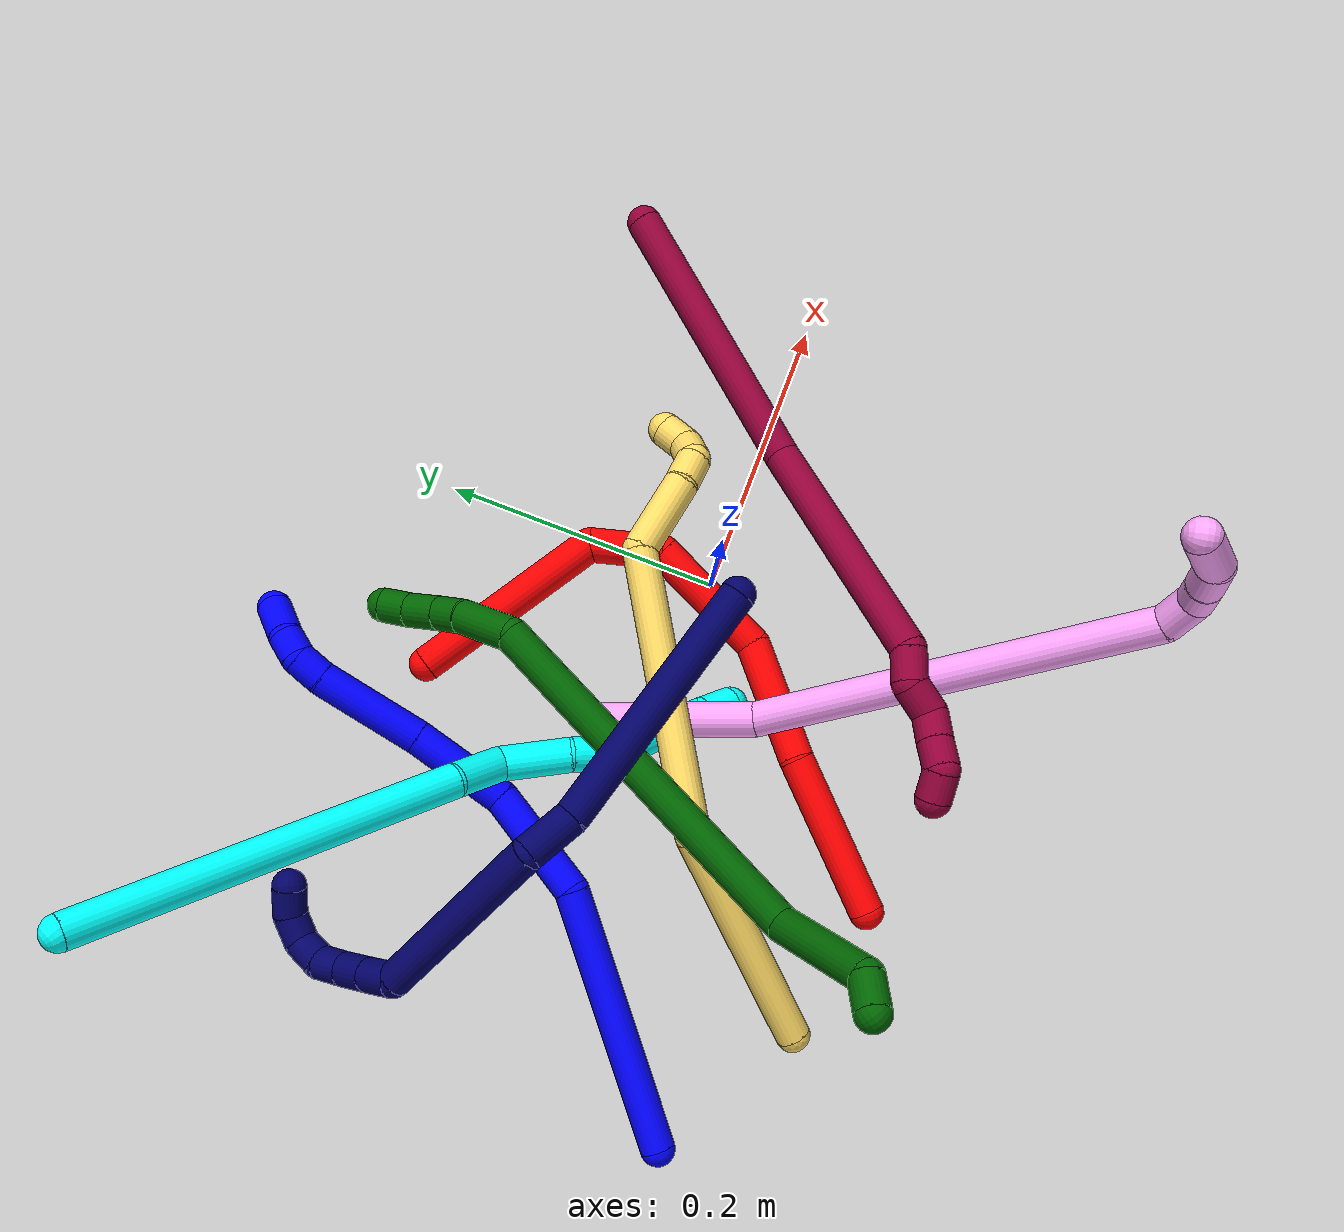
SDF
<sdf version="1.7">
 <world name="default">
  <plugin name="TubeGeneratorPlugin" filename="libtube_generator_plugin.so"/>
  <model name="photoneo_s_sensor">
   <static>1</static>
   <pose>0 0 2 1.57079 1.57079 3.14159</pose>
   <link name="link">
    <inertial><mass>0.1</mass></inertial>
    <sensor name="sensor" type="depth">
     <update_rate>30</update_rate>
     <camera>
      <horizontal_fov>1.22</horizontal_fov>
      <image><width>1920</width><height>1200</height><format>B8G8R8</format></image>
      <clip><near>0.1</near><far>4</far></clip>
      <depth_camera><output>points</output></depth_camera>
     </camera>
     <plugin name="camera_plugin" filename="libgazebo_ros_depth_camera.so">
      <baseline>0.2</baseline>
      <alwaysOn>1</alwaysOn>
      <updateRate>0.0</updateRate>
      <cameraName>camera_ir</cameraName>
      <imageTopicName>/camera/color/image_raw</imageTopicName>
      <cameraInfoTopicName>/camera/color/camera_info</cameraInfoTopicName>
      <depthImageTopicName>/camera/depth/image_raw</depthImageTopicName>
      <depthImageCameraInfoTopicName>/camera/depth/camera_info</depthImageCameraInfoTopicName>
      <pointCloudTopicName>/camera/depth/points</pointCloudTopicName>
      <frameName>fr_optical</frameName>
      <pointCloudCutoff>0.1</pointCloudCutoff>
      <pointCloudCutoffMax>2.0</pointCloudCutoffMax>
      <distortionK1>0</distortionK1>
      <distortionK2>0</distortionK2>
      <distortionK3>0</distortionK3>
      <distortionT1>0</distortionT1>
      <distortionT2>0</distortionT2>
      <CxPrime>0</CxPrime>
      <Cx>0</Cx>
      <Cy>0</Cy>
      <focalLength>0</focalLength>
      <hackBaseline>0</hackBaseline>
     </plugin>
    </sensor>
   </link>
  </model>
  <gravity>0 0 -9.8</gravity>
  <magnetic_field>6e-06 2.3e-05 -4.2e-05</magnetic_field>
  <atmosphere type="adiabatic"/>
  <physics name="default_physics" default="0" type="ode">
   <max_step_size>0.003</max_step_size>
   <real_time_factor>1</real_time_factor>
   <real_time_update_rate>1000</real_time_update_rate>
   <max_contacts>10000</max_contacts>
   <ode>
    <solver>
     <type>quick</type>
     <iters>100</iters>
     <sor>1.3</sor>
     <use_dynamic_moi_rescaling>0</use_dynamic_moi_rescaling>
    </solver>
    <constraints>
     <contact_max_correcting_vel>0</contact_max_correcting_vel>
     <contact_surface_layer>0.001</contact_surface_layer>
     <cfm>0</cfm>
     <erp>0.2</erp>
    </constraints>
   </ode>
  </physics>
  <scene><ambient>0.4 0.4 0.4 1</ambient><background>0.7 0.7 0.7 1</background><shadows>0</shadows></scene>
  <audio><device>default</device></audio>
  <spherical_coordinates>
   <surface_model>EARTH_WGS84</surface_model>
   <latitude_deg>0</latitude_deg>
   <longitude_deg>0</longitude_deg>
   <elevation>0</elevation>
   <heading_deg>0</heading_deg>
  </spherical_coordinates>
  <model name="bin">
   <static>1</static>
   <link name="bottom">
    <collision name="collision-bottom">
     <pose>0 0 -0.01 0 -0 0</pose>
     <geometry><box><size>0.8 0.6 0.02</size></box></geometry>
     <surface>
      <friction><ode><mu>100</mu><mu2>100</mu2></ode></friction>
      <contact><collide_bitmask>65535</collide_bitmask></contact>
     </surface>
    </collision>
   </link>
   <link name="west_wall">
    <collision name="collision-west_wall">
     <pose>-0.41 0 0.1 0 -0 0</pose>
     <geometry><box><size>0.02 0.6 0.2</size></box></geometry>
     <surface>
      <friction><ode><mu>100</mu><mu2>100</mu2></ode></friction>
      <contact><collide_bitmask>65535</collide_bitmask></contact>
     </surface>
    </collision>
   </link>
   <link name="east_wall">
    <collision name="collision-east_wall">
     <pose>0.41 0 0.1 0 -0 0</pose>
     <geometry><box><size>0.02 0.6 0.2</size></box></geometry>
     <surface>
      <friction><ode><mu>100</mu><mu2>100</mu2></ode></friction>
      <contact><collide_bitmask>65535</collide_bitmask></contact>
     </surface>
    </collision>
   </link>
   <link name="south_wall">
    <collision name="collision-south_wall">
     <pose>0 -0.31 0.1 0 -0 0</pose>
     <geometry><box><size>0.8 0.02 0.2</size></box></geometry>
     <surface>
      <friction><ode><mu>100</mu><mu2>100</mu2></ode></friction>
      <contact><collide_bitmask>65535</collide_bitmask></contact>
     </surface>
    </collision>
   </link>
   <link name="north_wall">
    <collision name="collision-north_wall">
     <pose>0 0.31 0.1 0 -0 0</pose>
     <geometry><box><size>0.8 0.02 0.2</size></box></geometry>
     <surface>
      <friction><ode><mu>100</mu><mu2>100</mu2></ode></friction>
      <contact><collide_bitmask>65535</collide_bitmask></contact>
     </surface>
    </collision>
   </link>
  </model>
  <model name="1">
   <static>0</static>
   <link name="1">
    <collision name="collision-cylinder-e_1_1_4">
     <pose>0.008089 0.071537 0.062962 -0.849069 0.084673 -0.038292</pose>
     <geometry><cylinder><radius>0.0125</radius><length>0.191282</length></cylinder></geometry>
     <surface>
      <friction><ode><mu>1.16</mu><mu2>1.16</mu2><slip1>0</slip1><slip2>0</slip2></ode></friction>
      <contact><ode><kp>1e+06</kp><kd>1</kd><max_vel>0</max_vel><min_depth>0.001</min_depth></ode></contact>
     </surface>
    </collision>
    <visual name="visual-cylinder-e_1_1_4">
     <pose>0.008089 0.071537 0.062962 -0.849069 0.084673 -0.038292</pose>
     <geometry><cylinder><radius>0.0125</radius><length>0.191282</length></cylinder></geometry>
     <material><ambient>0 0 1 1</ambient></material>
    </visual>
    <collision name="collision-cylinder-e_2_4_5">
     <pose>0.030526 0.162402 0.160155 -0.513984 0.349993 -0.092863</pose>
     <geometry><cylinder><radius>0.0125</radius><length>0.083695</length></cylinder></geometry>
     <surface>
      <friction><ode><mu>1.16</mu><mu2>1.16</mu2><slip1>0</slip1><slip2>0</slip2></ode></friction>
      <contact><ode><kp>1e+06</kp><kd>1</kd><max_vel>0</max_vel><min_depth>0.001</min_depth></ode></contact>
     </surface>
    </collision>
    <visual name="visual-cylinder-e_2_4_5">
     <pose>0.030526 0.162402 0.160155 -0.513984 0.349993 -0.092863</pose>
     <geometry><cylinder><radius>0.0125</radius><length>0.083695</length></cylinder></geometry>
     <material><ambient>0 0 1 1</ambient></material>
    </visual>
    <collision name="collision-cylinder-e_3_5_6">
     <pose>0.068295 0.199394 0.21668 -0.67009 0.68881 -0.248492</pose>
     <geometry><cylinder><radius>0.0125</radius><length>0.07369</length></cylinder></geometry>
     <surface>
      <friction><ode><mu>1.16</mu><mu2>1.16</mu2><slip1>0</slip1><slip2>0</slip2></ode></friction>
      <contact><ode><kp>1e+06</kp><kd>1</kd><max_vel>0</max_vel><min_depth>0.001</min_depth></ode></contact>
     </surface>
    </collision>
    <visual name="visual-cylinder-e_3_5_6">
     <pose>0.068295 0.199394 0.21668 -0.67009 0.68881 -0.248492</pose>
     <geometry><cylinder><radius>0.0125</radius><length>0.07369</length></cylinder></geometry>
     <material><ambient>0 0 1 1</ambient></material>
    </visual>
    <collision name="collision-cylinder-e_4_6_7">
     <pose>0.119433 0.235819 0.26062 -0.714079 0.768999 -0.299621</pose>
     <geometry><cylinder><radius>0.0125</radius><length>0.079719</length></cylinder></geometry>
     <surface>
      <friction><ode><mu>1.16</mu><mu2>1.16</mu2><slip1>0</slip1><slip2>0</slip2></ode></friction>
      <contact><ode><kp>1e+06</kp><kd>1</kd><max_vel>0</max_vel><min_depth>0.001</min_depth></ode></contact>
     </surface>
    </collision>
    <visual name="visual-cylinder-e_4_6_7">
     <pose>0.119433 0.235819 0.26062 -0.714079 0.768999 -0.299621</pose>
     <geometry><cylinder><radius>0.0125</radius><length>0.079719</length></cylinder></geometry>
     <material><ambient>0 0 1 1</ambient></material>
    </visual>
    <collision name="collision-cylinder-e_5_7_8">
     <pose>0.1534 0.260559 0.288981 -0.727609 0.60721 -0.23745</pose>
     <geometry><cylinder><radius>0.0125</radius><length>0.0219</length></cylinder></geometry>
     <surface>
      <friction><ode><mu>1.16</mu><mu2>1.16</mu2><slip1>0</slip1><slip2>0</slip2></ode></friction>
      <contact><ode><kp>1e+06</kp><kd>1</kd><max_vel>0</max_vel><min_depth>0.001</min_depth></ode></contact>
     </surface>
    </collision>
    <visual name="visual-cylinder-e_5_7_8">
     <pose>0.1534 0.260559 0.288981 -0.727609 0.60721 -0.23745</pose>
     <geometry><cylinder><radius>0.0125</radius><length>0.0219</length></cylinder></geometry>
     <material><ambient>0 0 1 1</ambient></material>
    </visual>
    <collision name="collision-cylinder-e_6_8_9">
     <pose>0.161916 0.270766 0.3046 -0.443152 0.226223 -0.05117</pose>
     <geometry><cylinder><radius>0.0125</radius><length>0.020228</length></cylinder></geometry>
     <surface>
      <friction><ode><mu>1.16</mu><mu2>1.16</mu2><slip1>0</slip1><slip2>0</slip2></ode></friction>
      <contact><ode><kp>1e+06</kp><kd>1</kd><max_vel>0</max_vel><min_depth>0.001</min_depth></ode></contact>
     </surface>
    </collision>
    <visual name="visual-cylinder-e_6_8_9">
     <pose>0.161916 0.270766 0.3046 -0.443152 0.226223 -0.05117</pose>
     <geometry><cylinder><radius>0.0125</radius><length>0.020228</length></cylinder></geometry>
     <material><ambient>0 0 1 1</ambient></material>
    </visual>
    <collision name="collision-cylinder-e_7_9_2">
     <pose>0.165082 0.277436 0.328016 -0.166894 0.060954 -0.0051</pose>
     <geometry><cylinder><radius>0.0125</radius><length>0.029487</length></cylinder></geometry>
     <surface>
      <friction><ode><mu>1.16</mu><mu2>1.16</mu2><slip1>0</slip1><slip2>0</slip2></ode></friction>
      <contact><ode><kp>1e+06</kp><kd>1</kd><max_vel>0</max_vel><min_depth>0.001</min_depth></ode></contact>
     </surface>
    </collision>
    <visual name="visual-cylinder-e_7_9_2">
     <pose>0.165082 0.277436 0.328016 -0.166894 0.060954 -0.0051</pose>
     <geometry><cylinder><radius>0.0125</radius><length>0.029487</length></cylinder></geometry>
     <material><ambient>0 0 1 1</ambient></material>
    </visual>
    <collision name="collision-sphere-2">
     <pose>0.165981 0.279881 0.342527 0 -0 0</pose>
     <geometry><sphere><radius>0.0125</radius></sphere></geometry>
     <surface>
      <friction><ode><mu>1.16</mu><mu2>1.16</mu2><slip1>0</slip1><slip2>0</slip2></ode></friction>
      <contact><ode><kp>1e+06</kp><kd>1</kd><max_vel>0</max_vel><min_depth>0.001</min_depth></ode></contact>
     </surface>
    </collision>
    <visual name="visual-sphere-2">
     <pose>0.165981 0.279881 0.342527 0 -0 0</pose>
     <geometry><sphere><radius>0.0125</radius></sphere></geometry>
     <material><ambient>0 0 1 1</ambient></material>
    </visual>
    <collision name="collision-sphere-9">
     <pose>0.164184 0.274992 0.313504 0 -0 0</pose>
     <geometry><sphere><radius>0.0125</radius></sphere></geometry>
     <surface>
      <friction><ode><mu>1.16</mu><mu2>1.16</mu2><slip1>0</slip1><slip2>0</slip2></ode></friction>
      <contact><ode><kp>1e+06</kp><kd>1</kd><max_vel>0</max_vel><min_depth>0.001</min_depth></ode></contact>
     </surface>
    </collision>
    <visual name="visual-sphere-9">
     <pose>0.164184 0.274992 0.313504 0 -0 0</pose>
     <geometry><sphere><radius>0.0125</radius></sphere></geometry>
     <material><ambient>0 0 1 1</ambient></material>
    </visual>
    <collision name="collision-sphere-4">
     <pose>0.016177 0.143074 0.125924 0 -0 0</pose>
     <geometry><sphere><radius>0.0125</radius></sphere></geometry>
     <surface>
      <friction><ode><mu>1.16</mu><mu2>1.16</mu2><slip1>0</slip1><slip2>0</slip2></ode></friction>
      <contact><ode><kp>1e+06</kp><kd>1</kd><max_vel>0</max_vel><min_depth>0.001</min_depth></ode></contact>
     </surface>
    </collision>
    <visual name="visual-sphere-4">
     <pose>0.016177 0.143074 0.125924 0 -0 0</pose>
     <geometry><sphere><radius>0.0125</radius></sphere></geometry>
     <material><ambient>0 0 1 1</ambient></material>
    </visual>
    <collision name="collision-sphere-1">
     <geometry><sphere><radius>0.0125</radius></sphere></geometry>
     <surface>
      <friction><ode><mu>1.16</mu><mu2>1.16</mu2><slip1>0</slip1><slip2>0</slip2></ode></friction>
      <contact><ode><kp>1e+06</kp><kd>1</kd><max_vel>0</max_vel><min_depth>0.001</min_depth></ode></contact>
     </surface>
    </collision>
    <visual name="visual-sphere-1">
     <geometry><sphere><radius>0.0125</radius></sphere></geometry>
     <material><ambient>0 0 1 1</ambient></material>
    </visual>
    <collision name="collision-sphere-8">
     <pose>0.159647 0.266539 0.295696 0 -0 0</pose>
     <geometry><sphere><radius>0.0125</radius></sphere></geometry>
     <surface>
      <friction><ode><mu>1.16</mu><mu2>1.16</mu2><slip1>0</slip1><slip2>0</slip2></ode></friction>
      <contact><ode><kp>1e+06</kp><kd>1</kd><max_vel>0</max_vel><min_depth>0.001</min_depth></ode></contact>
     </surface>
    </collision>
    <visual name="visual-sphere-8">
     <pose>0.159647 0.266539 0.295696 0 -0 0</pose>
     <geometry><sphere><radius>0.0125</radius></sphere></geometry>
     <material><ambient>0 0 1 1</ambient></material>
    </visual>
    <collision name="collision-sphere-5">
     <pose>0.044876 0.181729 0.194387 0 -0 0</pose>
     <geometry><sphere><radius>0.0125</radius></sphere></geometry>
     <surface>
      <friction><ode><mu>1.16</mu><mu2>1.16</mu2><slip1>0</slip1><slip2>0</slip2></ode></friction>
      <contact><ode><kp>1e+06</kp><kd>1</kd><max_vel>0</max_vel><min_depth>0.001</min_depth></ode></contact>
     </surface>
    </collision>
    <visual name="visual-sphere-5">
     <pose>0.044876 0.181729 0.194387 0 -0 0</pose>
     <geometry><sphere><radius>0.0125</radius></sphere></geometry>
     <material><ambient>0 0 1 1</ambient></material>
    </visual>
    <collision name="collision-sphere-6">
     <pose>0.091714 0.21706 0.238974 0 -0 0</pose>
     <geometry><sphere><radius>0.0125</radius></sphere></geometry>
     <surface>
      <friction><ode><mu>1.16</mu><mu2>1.16</mu2><slip1>0</slip1><slip2>0</slip2></ode></friction>
      <contact><ode><kp>1e+06</kp><kd>1</kd><max_vel>0</max_vel><min_depth>0.001</min_depth></ode></contact>
     </surface>
    </collision>
    <visual name="visual-sphere-6">
     <pose>0.091714 0.21706 0.238974 0 -0 0</pose>
     <geometry><sphere><radius>0.0125</radius></sphere></geometry>
     <material><ambient>0 0 1 1</ambient></material>
    </visual>
    <collision name="collision-sphere-7">
     <pose>0.147152 0.254578 0.282265 0 -0 0</pose>
     <geometry><sphere><radius>0.0125</radius></sphere></geometry>
     <surface>
      <friction><ode><mu>1.16</mu><mu2>1.16</mu2><slip1>0</slip1><slip2>0</slip2></ode></friction>
      <contact><ode><kp>1e+06</kp><kd>1</kd><max_vel>0</max_vel><min_depth>0.001</min_depth></ode></contact>
     </surface>
    </collision>
    <visual name="visual-sphere-7">
     <pose>0.147152 0.254578 0.282265 0 -0 0</pose>
     <geometry><sphere><radius>0.0125</radius></sphere></geometry>
     <material><ambient>0 0 1 1</ambient></material>
    </visual>
    <inertial>
     <pose>0.060316 0.160265 0.168706 0 -0 0</pose>
     <mass>0.5</mass>
     <inertia>
      <ixx>0.00067</ixx>
      <ixy>0</ixy>
      <ixz>0</ixz>
      <iyy>0.000491</iyy>
      <iyz>0</iyz>
      <izz>-0.000604</izz>
     </inertia>
    </inertial>
   </link>
   <pose>-0.388241 -0.106648 0.012294 2.34089 -0.220796 2.19236</pose>
  </model>
  <model name="2">
   <static>0</static>
   <link name="2">
    <collision name="collision-cylinder-e_1_1_4">
     <pose>0.024405 0.009519 -0.068071 -3.00265 0.341184 -2.37383</pose>
     <geometry><cylinder><radius>0.0125</radius><length>0.145875</length></cylinder></geometry>
     <surface>
      <friction><ode><mu>1.16</mu><mu2>1.16</mu2><slip1>0</slip1><slip2>0</slip2></ode></friction>
      <contact><ode><kp>1e+06</kp><kd>1</kd><max_vel>0</max_vel><min_depth>0.001</min_depth></ode></contact>
     </surface>
    </collision>
    <visual name="visual-cylinder-e_1_1_4">
     <pose>0.024405 0.009519 -0.068071 -3.00265 0.341184 -2.37383</pose>
     <geometry><cylinder><radius>0.0125</radius><length>0.145875</length></cylinder></geometry>
     <material><ambient>1 0 0 1</ambient></material>
    </visual>
    <collision name="collision-cylinder-e_2_4_5">
     <pose>0.049764 0.005208 -0.158752 2.59263 0.035986 0.127635</pose>
     <geometry><cylinder><radius>0.0125</radius><length>0.053043</length></cylinder></geometry>
     <surface>
      <friction><ode><mu>1.16</mu><mu2>1.16</mu2><slip1>0</slip1><slip2>0</slip2></ode></friction>
      <contact><ode><kp>1e+06</kp><kd>1</kd><max_vel>0</max_vel><min_depth>0.001</min_depth></ode></contact>
     </surface>
    </collision>
    <visual name="visual-cylinder-e_2_4_5">
     <pose>0.049764 0.005208 -0.158752 2.59263 0.035986 0.127635</pose>
     <geometry><cylinder><radius>0.0125</radius><length>0.053043</length></cylinder></geometry>
     <material><ambient>1 0 0 1</ambient></material>
    </visual>
    <collision name="collision-cylinder-e_3_5_6">
     <pose>0.035 -0.048473 -0.199524 1.99843 -0.344603 -0.528476</pose>
     <geometry><cylinder><radius>0.0125</radius><length>0.093059</length></cylinder></geometry>
     <surface>
      <friction><ode><mu>1.16</mu><mu2>1.16</mu2><slip1>0</slip1><slip2>0</slip2></ode></friction>
      <contact><ode><kp>1e+06</kp><kd>1</kd><max_vel>0</max_vel><min_depth>0.001</min_depth></ode></contact>
     </surface>
    </collision>
    <visual name="visual-cylinder-e_3_5_6">
     <pose>0.035 -0.048473 -0.199524 1.99843 -0.344603 -0.528476</pose>
     <geometry><cylinder><radius>0.0125</radius><length>0.093059</length></cylinder></geometry>
     <material><ambient>1 0 0 1</ambient></material>
    </visual>
    <collision name="collision-cylinder-e_4_6_7">
     <pose>0.007929 -0.131804 -0.21422 1.49125 -0.254602 -0.235301</pose>
     <geometry><cylinder><radius>0.0125</radius><length>0.090143</length></cylinder></geometry>
     <surface>
      <friction><ode><mu>1.16</mu><mu2>1.16</mu2><slip1>0</slip1><slip2>0</slip2></ode></friction>
      <contact><ode><kp>1e+06</kp><kd>1</kd><max_vel>0</max_vel><min_depth>0.001</min_depth></ode></contact>
     </surface>
    </collision>
    <visual name="visual-cylinder-e_4_6_7">
     <pose>0.007929 -0.131804 -0.21422 1.49125 -0.254602 -0.235301</pose>
     <geometry><cylinder><radius>0.0125</radius><length>0.090143</length></cylinder></geometry>
     <material><ambient>1 0 0 1</ambient></material>
    </visual>
    <collision name="collision-cylinder-e_5_7_2">
     <pose>-0.028571 -0.228477 -0.214228 1.63601 -0.44082 -0.469499</pose>
     <geometry><cylinder><radius>0.0125</radius><length>0.11788</length></cylinder></geometry>
     <surface>
      <friction><ode><mu>1.16</mu><mu2>1.16</mu2><slip1>0</slip1><slip2>0</slip2></ode></friction>
      <contact><ode><kp>1e+06</kp><kd>1</kd><max_vel>0</max_vel><min_depth>0.001</min_depth></ode></contact>
     </surface>
    </collision>
    <visual name="visual-cylinder-e_5_7_2">
     <pose>-0.028571 -0.228477 -0.214228 1.63601 -0.44082 -0.469499</pose>
     <geometry><cylinder><radius>0.0125</radius><length>0.11788</length></cylinder></geometry>
     <material><ambient>1 0 0 1</ambient></material>
    </visual>
    <collision name="collision-sphere-2">
     <pose>-0.05372 -0.281669 -0.217702 0 -0 0</pose>
     <geometry><sphere><radius>0.0125</radius></sphere></geometry>
     <surface>
      <friction><ode><mu>1.16</mu><mu2>1.16</mu2><slip1>0</slip1><slip2>0</slip2></ode></friction>
      <contact><ode><kp>1e+06</kp><kd>1</kd><max_vel>0</max_vel><min_depth>0.001</min_depth></ode></contact>
     </surface>
    </collision>
    <visual name="visual-sphere-2">
     <pose>-0.05372 -0.281669 -0.217702 0 -0 0</pose>
     <geometry><sphere><radius>0.0125</radius></sphere></geometry>
     <material><ambient>1 0 0 1</ambient></material>
    </visual>
    <collision name="collision-sphere-7">
     <pose>-0.003423 -0.175285 -0.210754 0 -0 0</pose>
     <geometry><sphere><radius>0.0125</radius></sphere></geometry>
     <surface>
      <friction><ode><mu>1.16</mu><mu2>1.16</mu2><slip1>0</slip1><slip2>0</slip2></ode></friction>
      <contact><ode><kp>1e+06</kp><kd>1</kd><max_vel>0</max_vel><min_depth>0.001</min_depth></ode></contact>
     </surface>
    </collision>
    <visual name="visual-sphere-7">
     <pose>-0.003423 -0.175285 -0.210754 0 -0 0</pose>
     <geometry><sphere><radius>0.0125</radius></sphere></geometry>
     <material><ambient>1 0 0 1</ambient></material>
    </visual>
    <collision name="collision-sphere-6">
     <pose>0.019281 -0.088323 -0.217686 0 -0 0</pose>
     <geometry><sphere><radius>0.0125</radius></sphere></geometry>
     <surface>
      <friction><ode><mu>1.16</mu><mu2>1.16</mu2><slip1>0</slip1><slip2>0</slip2></ode></friction>
      <contact><ode><kp>1e+06</kp><kd>1</kd><max_vel>0</max_vel><min_depth>0.001</min_depth></ode></contact>
     </surface>
    </collision>
    <visual name="visual-sphere-6">
     <pose>0.019281 -0.088323 -0.217686 0 -0 0</pose>
     <geometry><sphere><radius>0.0125</radius></sphere></geometry>
     <material><ambient>1 0 0 1</ambient></material>
    </visual>
    <collision name="collision-sphere-5">
     <pose>0.050718 -0.008622 -0.181361 0 -0 0</pose>
     <geometry><sphere><radius>0.0125</radius></sphere></geometry>
     <surface>
      <friction><ode><mu>1.16</mu><mu2>1.16</mu2><slip1>0</slip1><slip2>0</slip2></ode></friction>
      <contact><ode><kp>1e+06</kp><kd>1</kd><max_vel>0</max_vel><min_depth>0.001</min_depth></ode></contact>
     </surface>
    </collision>
    <visual name="visual-sphere-5">
     <pose>0.050718 -0.008622 -0.181361 0 -0 0</pose>
     <geometry><sphere><radius>0.0125</radius></sphere></geometry>
     <material><ambient>1 0 0 1</ambient></material>
    </visual>
    <collision name="collision-sphere-1">
     <geometry><sphere><radius>0.0125</radius></sphere></geometry>
     <surface>
      <friction><ode><mu>1.16</mu><mu2>1.16</mu2><slip1>0</slip1><slip2>0</slip2></ode></friction>
      <contact><ode><kp>1e+06</kp><kd>1</kd><max_vel>0</max_vel><min_depth>0.001</min_depth></ode></contact>
     </surface>
    </collision>
    <visual name="visual-sphere-1">
     <geometry><sphere><radius>0.0125</radius></sphere></geometry>
     <material><ambient>1 0 0 1</ambient></material>
    </visual>
    <collision name="collision-sphere-4">
     <pose>0.04881 0.019038 -0.136142 0 -0 0</pose>
     <geometry><sphere><radius>0.0125</radius></sphere></geometry>
     <surface>
      <friction><ode><mu>1.16</mu><mu2>1.16</mu2><slip1>0</slip1><slip2>0</slip2></ode></friction>
      <contact><ode><kp>1e+06</kp><kd>1</kd><max_vel>0</max_vel><min_depth>0.001</min_depth></ode></contact>
     </surface>
    </collision>
    <visual name="visual-sphere-4">
     <pose>0.04881 0.019038 -0.136142 0 -0 0</pose>
     <geometry><sphere><radius>0.0125</radius></sphere></geometry>
     <material><ambient>1 0 0 1</ambient></material>
    </visual>
    <inertial>
     <pose>0.013607 -0.08332 -0.162963 0 -0 0</pose>
     <mass>0.5</mass>
     <inertia>
      <ixx>-0.000214</ixx>
      <ixy>0</ixy>
      <ixz>0</ixz>
      <iyy>-0.000101</iyy>
      <iyz>0</iyz>
      <izz>0.000218</izz>
     </inertia>
    </inertial>
   </link>
   <pose>-0.127747 0.170941 0.012446 -1.02322 -1.0963 0.243867</pose>
  </model>
  <model name="3">
   <static>0</static>
   <link name="3">
    <collision name="collision-cylinder-e_1_1_4">
     <pose>0.014073 -0.039694 -0.132523 2.85057 0.101377 0.666541</pose>
     <geometry><cylinder><radius>0.0125</radius><length>0.278109</length></cylinder></geometry>
     <surface>
      <friction><ode><mu>1.16</mu><mu2>1.16</mu2><slip1>0</slip1><slip2>0</slip2></ode></friction>
      <contact><ode><kp>1e+06</kp><kd>1</kd><max_vel>0</max_vel><min_depth>0.001</min_depth></ode></contact>
     </surface>
    </collision>
    <visual name="visual-cylinder-e_1_1_4">
     <pose>0.014073 -0.039694 -0.132523 2.85057 0.101377 0.666541</pose>
     <geometry><cylinder><radius>0.0125</radius><length>0.278109</length></cylinder></geometry>
     <material><ambient>0.003922 1 0.996078 1</ambient></material>
    </visual>
    <collision name="collision-cylinder-e_2_4_5">
     <pose>0.026591 -0.088929 -0.283732 2.66953 -0.073979 -0.305332</pose>
     <geometry><cylinder><radius>0.0125</radius><length>0.042075</length></cylinder></geometry>
     <surface>
      <friction><ode><mu>1.16</mu><mu2>1.16</mu2><slip1>0</slip1><slip2>0</slip2></ode></friction>
      <contact><ode><kp>1e+06</kp><kd>1</kd><max_vel>0</max_vel><min_depth>0.001</min_depth></ode></contact>
     </surface>
    </collision>
    <visual name="visual-cylinder-e_2_4_5">
     <pose>0.026591 -0.088929 -0.283732 2.66953 -0.073979 -0.305332</pose>
     <geometry><cylinder><radius>0.0125</radius><length>0.042075</length></cylinder></geometry>
     <material><ambient>0.003922 1 0.996078 1</ambient></material>
    </visual>
    <collision name="collision-cylinder-e_3_5_6">
     <pose>0.039251 -0.101252 -0.32297 3.00697 0.600848 2.71308</pose>
     <geometry><cylinder><radius>0.0125</radius><length>0.050287</length></cylinder></geometry>
     <surface>
      <friction><ode><mu>1.16</mu><mu2>1.16</mu2><slip1>0</slip1><slip2>0</slip2></ode></friction>
      <contact><ode><kp>1e+06</kp><kd>1</kd><max_vel>0</max_vel><min_depth>0.001</min_depth></ode></contact>
     </surface>
    </collision>
    <visual name="visual-cylinder-e_3_5_6">
     <pose>0.039251 -0.101252 -0.32297 3.00697 0.600848 2.71308</pose>
     <geometry><cylinder><radius>0.0125</radius><length>0.050287</length></cylinder></geometry>
     <material><ambient>0.003922 1 0.996078 1</ambient></material>
    </visual>
    <collision name="collision-cylinder-e_4_6_7">
     <pose>0.060805 -0.109079 -0.356427 2.76909 0.487167 1.8441</pose>
     <geometry><cylinder><radius>0.0125</radius><length>0.031359</length></cylinder></geometry>
     <surface>
      <friction><ode><mu>1.16</mu><mu2>1.16</mu2><slip1>0</slip1><slip2>0</slip2></ode></friction>
      <contact><ode><kp>1e+06</kp><kd>1</kd><max_vel>0</max_vel><min_depth>0.001</min_depth></ode></contact>
     </surface>
    </collision>
    <visual name="visual-cylinder-e_4_6_7">
     <pose>0.060805 -0.109079 -0.356427 2.76909 0.487167 1.8441</pose>
     <geometry><cylinder><radius>0.0125</radius><length>0.031359</length></cylinder></geometry>
     <material><ambient>0.003922 1 0.996078 1</ambient></material>
    </visual>
    <collision name="collision-cylinder-e_5_7_8">
     <pose>0.069212 -0.11887 -0.387629 2.88764 0.056347 0.434516</pose>
     <geometry><cylinder><radius>0.0125</radius><length>0.037866</length></cylinder></geometry>
     <surface>
      <friction><ode><mu>1.16</mu><mu2>1.16</mu2><slip1>0</slip1><slip2>0</slip2></ode></friction>
      <contact><ode><kp>1e+06</kp><kd>1</kd><max_vel>0</max_vel><min_depth>0.001</min_depth></ode></contact>
     </surface>
    </collision>
    <visual name="visual-cylinder-e_5_7_8">
     <pose>0.069212 -0.11887 -0.387629 2.88764 0.056347 0.434516</pose>
     <geometry><cylinder><radius>0.0125</radius><length>0.037866</length></cylinder></geometry>
     <material><ambient>0.003922 1 0.996078 1</ambient></material>
    </visual>
    <collision name="collision-cylinder-e_6_8_9">
     <pose>0.078829 -0.120765 -0.421247 -2.95741 0.501851 -2.44997</pose>
     <geometry><cylinder><radius>0.0125</radius><length>0.035553</length></cylinder></geometry>
     <surface>
      <friction><ode><mu>1.16</mu><mu2>1.16</mu2><slip1>0</slip1><slip2>0</slip2></ode></friction>
      <contact><ode><kp>1e+06</kp><kd>1</kd><max_vel>0</max_vel><min_depth>0.001</min_depth></ode></contact>
     </surface>
    </collision>
    <visual name="visual-cylinder-e_6_8_9">
     <pose>0.078829 -0.120765 -0.421247 -2.95741 0.501851 -2.44997</pose>
     <geometry><cylinder><radius>0.0125</radius><length>0.035553</length></cylinder></geometry>
     <material><ambient>0.003922 1 0.996078 1</ambient></material>
    </visual>
    <collision name="collision-cylinder-e_7_9_2">
     <pose>0.088291 -0.121989 -0.448217 2.80483 0.073635 0.426766</pose>
     <geometry><cylinder><radius>0.0125</radius><length>0.02475</length></cylinder></geometry>
     <surface>
      <friction><ode><mu>1.16</mu><mu2>1.16</mu2><slip1>0</slip1><slip2>0</slip2></ode></friction>
      <contact><ode><kp>1e+06</kp><kd>1</kd><max_vel>0</max_vel><min_depth>0.001</min_depth></ode></contact>
     </surface>
    </collision>
    <visual name="visual-cylinder-e_7_9_2">
     <pose>0.088291 -0.121989 -0.448217 2.80483 0.073635 0.426766</pose>
     <geometry><cylinder><radius>0.0125</radius><length>0.02475</length></cylinder></geometry>
     <material><ambient>0.003922 1 0.996078 1</ambient></material>
    </visual>
    <collision name="collision-sphere-2">
     <pose>0.089202 -0.126067 -0.459865 0 -0 0</pose>
     <geometry><sphere><radius>0.0125</radius></sphere></geometry>
     <surface>
      <friction><ode><mu>1.16</mu><mu2>1.16</mu2><slip1>0</slip1><slip2>0</slip2></ode></friction>
      <contact><ode><kp>1e+06</kp><kd>1</kd><max_vel>0</max_vel><min_depth>0.001</min_depth></ode></contact>
     </surface>
    </collision>
    <visual name="visual-sphere-2">
     <pose>0.089202 -0.126067 -0.459865 0 -0 0</pose>
     <geometry><sphere><radius>0.0125</radius></sphere></geometry>
     <material><ambient>0.003922 1 0.996078 1</ambient></material>
    </visual>
    <collision name="collision-sphere-9">
     <pose>0.087381 -0.117911 -0.436568 0 -0 0</pose>
     <geometry><sphere><radius>0.0125</radius></sphere></geometry>
     <surface>
      <friction><ode><mu>1.16</mu><mu2>1.16</mu2><slip1>0</slip1><slip2>0</slip2></ode></friction>
      <contact><ode><kp>1e+06</kp><kd>1</kd><max_vel>0</max_vel><min_depth>0.001</min_depth></ode></contact>
     </surface>
    </collision>
    <visual name="visual-sphere-9">
     <pose>0.087381 -0.117911 -0.436568 0 -0 0</pose>
     <geometry><sphere><radius>0.0125</radius></sphere></geometry>
     <material><ambient>0.003922 1 0.996078 1</ambient></material>
    </visual>
    <collision name="collision-sphere-4">
     <pose>0.028146 -0.079389 -0.265047 0 -0 0</pose>
     <geometry><sphere><radius>0.0125</radius></sphere></geometry>
     <surface>
      <friction><ode><mu>1.16</mu><mu2>1.16</mu2><slip1>0</slip1><slip2>0</slip2></ode></friction>
      <contact><ode><kp>1e+06</kp><kd>1</kd><max_vel>0</max_vel><min_depth>0.001</min_depth></ode></contact>
     </surface>
    </collision>
    <visual name="visual-sphere-4">
     <pose>0.028146 -0.079389 -0.265047 0 -0 0</pose>
     <geometry><sphere><radius>0.0125</radius></sphere></geometry>
     <material><ambient>0.003922 1 0.996078 1</ambient></material>
    </visual>
    <collision name="collision-sphere-1">
     <geometry><sphere><radius>0.0125</radius></sphere></geometry>
     <surface>
      <friction><ode><mu>1.16</mu><mu2>1.16</mu2><slip1>0</slip1><slip2>0</slip2></ode></friction>
      <contact><ode><kp>1e+06</kp><kd>1</kd><max_vel>0</max_vel><min_depth>0.001</min_depth></ode></contact>
     </surface>
    </collision>
    <visual name="visual-sphere-1">
     <geometry><sphere><radius>0.0125</radius></sphere></geometry>
     <material><ambient>0.003922 1 0.996078 1</ambient></material>
    </visual>
    <collision name="collision-sphere-8">
     <pose>0.070278 -0.123619 -0.405926 0 -0 0</pose>
     <geometry><sphere><radius>0.0125</radius></sphere></geometry>
     <surface>
      <friction><ode><mu>1.16</mu><mu2>1.16</mu2><slip1>0</slip1><slip2>0</slip2></ode></friction>
      <contact><ode><kp>1e+06</kp><kd>1</kd><max_vel>0</max_vel><min_depth>0.001</min_depth></ode></contact>
     </surface>
    </collision>
    <visual name="visual-sphere-8">
     <pose>0.070278 -0.123619 -0.405926 0 -0 0</pose>
     <geometry><sphere><radius>0.0125</radius></sphere></geometry>
     <material><ambient>0.003922 1 0.996078 1</ambient></material>
    </visual>
    <collision name="collision-sphere-5">
     <pose>0.025036 -0.098469 -0.302417 0 -0 0</pose>
     <geometry><sphere><radius>0.0125</radius></sphere></geometry>
     <surface>
      <friction><ode><mu>1.16</mu><mu2>1.16</mu2><slip1>0</slip1><slip2>0</slip2></ode></friction>
      <contact><ode><kp>1e+06</kp><kd>1</kd><max_vel>0</max_vel><min_depth>0.001</min_depth></ode></contact>
     </surface>
    </collision>
    <visual name="visual-sphere-5">
     <pose>0.025036 -0.098469 -0.302417 0 -0 0</pose>
     <geometry><sphere><radius>0.0125</radius></sphere></geometry>
     <material><ambient>0.003922 1 0.996078 1</ambient></material>
    </visual>
    <collision name="collision-sphere-6">
     <pose>0.053465 -0.104036 -0.343522 0 -0 0</pose>
     <geometry><sphere><radius>0.0125</radius></sphere></geometry>
     <surface>
      <friction><ode><mu>1.16</mu><mu2>1.16</mu2><slip1>0</slip1><slip2>0</slip2></ode></friction>
      <contact><ode><kp>1e+06</kp><kd>1</kd><max_vel>0</max_vel><min_depth>0.001</min_depth></ode></contact>
     </surface>
    </collision>
    <visual name="visual-sphere-6">
     <pose>0.053465 -0.104036 -0.343522 0 -0 0</pose>
     <geometry><sphere><radius>0.0125</radius></sphere></geometry>
     <material><ambient>0.003922 1 0.996078 1</ambient></material>
    </visual>
    <collision name="collision-sphere-7">
     <pose>0.068145 -0.114121 -0.369333 0 -0 0</pose>
     <geometry><sphere><radius>0.0125</radius></sphere></geometry>
     <surface>
      <friction><ode><mu>1.16</mu><mu2>1.16</mu2><slip1>0</slip1><slip2>0</slip2></ode></friction>
      <contact><ode><kp>1e+06</kp><kd>1</kd><max_vel>0</max_vel><min_depth>0.001</min_depth></ode></contact>
     </surface>
    </collision>
    <visual name="visual-sphere-7">
     <pose>0.068145 -0.114121 -0.369333 0 -0 0</pose>
     <geometry><sphere><radius>0.0125</radius></sphere></geometry>
     <material><ambient>0.003922 1 0.996078 1</ambient></material>
    </visual>
    <inertial>
     <pose>0.033044 -0.070215 -0.233921 0 -0 0</pose>
     <mass>0.5</mass>
     <inertia>
      <ixx>0.002533</ixx>
      <ixy>0</ixy>
      <ixz>0</ixz>
      <iyy>-0.000217</iyy>
      <iyz>0</iyz>
      <izz>0.000293</izz>
     </inertia>
    </inertial>
   </link>
   <pose>-0.36915 0.290698 0.206758 1.1845 -0.573322 -1.87226</pose>
  </model>
  <model name="4">
   <static>0</static>
   <link name="4">
    <collision name="collision-cylinder-e_1_1_4">
     <pose>-0.001293 -0.00941 0.05392 0.172783 -0.023622 -0.002046</pose>
     <geometry><cylinder><radius>0.0125</radius><length>0.109501</length></cylinder></geometry>
     <surface>
      <friction><ode><mu>1.16</mu><mu2>1.16</mu2><slip1>0</slip1><slip2>0</slip2></ode></friction>
      <contact><ode><kp>1e+06</kp><kd>1</kd><max_vel>0</max_vel><min_depth>0.001</min_depth></ode></contact>
     </surface>
    </collision>
    <visual name="visual-cylinder-e_1_1_4">
     <pose>-0.001293 -0.00941 0.05392 0.172783 -0.023622 -0.002046</pose>
     <geometry><cylinder><radius>0.0125</radius><length>0.109501</length></cylinder></geometry>
     <material><ambient>1 0.65098 0.996078 1</ambient></material>
    </visual>
    <collision name="collision-cylinder-e_2_4_5">
     <pose>0.058276 -0.069571 0.227264 0.401836 0.438577 0.090721</pose>
     <geometry><cylinder><radius>0.0125</radius><length>0.286647</length></cylinder></geometry>
     <surface>
      <friction><ode><mu>1.16</mu><mu2>1.16</mu2><slip1>0</slip1><slip2>0</slip2></ode></friction>
      <contact><ode><kp>1e+06</kp><kd>1</kd><max_vel>0</max_vel><min_depth>0.001</min_depth></ode></contact>
     </surface>
    </collision>
    <visual name="visual-cylinder-e_2_4_5">
     <pose>0.058276 -0.069571 0.227264 0.401836 0.438577 0.090721</pose>
     <geometry><cylinder><radius>0.0125</radius><length>0.286647</length></cylinder></geometry>
     <material><ambient>1 0.65098 0.996078 1</ambient></material>
    </visual>
    <collision name="collision-cylinder-e_3_5_6">
     <pose>0.127843 -0.128018 0.352278 0.942526 0.740968 0.390792</pose>
     <geometry><cylinder><radius>0.0125</radius><length>0.02579</length></cylinder></geometry>
     <surface>
      <friction><ode><mu>1.16</mu><mu2>1.16</mu2><slip1>0</slip1><slip2>0</slip2></ode></friction>
      <contact><ode><kp>1e+06</kp><kd>1</kd><max_vel>0</max_vel><min_depth>0.001</min_depth></ode></contact>
     </surface>
    </collision>
    <visual name="visual-cylinder-e_3_5_6">
     <pose>0.127843 -0.128018 0.352278 0.942526 0.740968 0.390792</pose>
     <geometry><cylinder><radius>0.0125</radius><length>0.02579</length></cylinder></geometry>
     <material><ambient>1 0.65098 0.996078 1</ambient></material>
    </visual>
    <collision name="collision-cylinder-e_4_6_7">
     <pose>0.146143 -0.139611 0.357319 1.7114 1.18172 1.3154</pose>
     <geometry><cylinder><radius>0.0125</radius><length>0.020744</length></cylinder></geometry>
     <surface>
      <friction><ode><mu>1.16</mu><mu2>1.16</mu2><slip1>0</slip1><slip2>0</slip2></ode></friction>
      <contact><ode><kp>1e+06</kp><kd>1</kd><max_vel>0</max_vel><min_depth>0.001</min_depth></ode></contact>
     </surface>
    </collision>
    <visual name="visual-cylinder-e_4_6_7">
     <pose>0.146143 -0.139611 0.357319 1.7114 1.18172 1.3154</pose>
     <geometry><cylinder><radius>0.0125</radius><length>0.020744</length></cylinder></geometry>
     <material><ambient>1 0.65098 0.996078 1</ambient></material>
    </visual>
    <collision name="collision-cylinder-e_5_7_8">
     <pose>0.166018 -0.148533 0.355992 1.72388 1.11124 1.25331</pose>
     <geometry><cylinder><radius>0.0125</radius><length>0.022935</length></cylinder></geometry>
     <surface>
      <friction><ode><mu>1.16</mu><mu2>1.16</mu2><slip1>0</slip1><slip2>0</slip2></ode></friction>
      <contact><ode><kp>1e+06</kp><kd>1</kd><max_vel>0</max_vel><min_depth>0.001</min_depth></ode></contact>
     </surface>
    </collision>
    <visual name="visual-cylinder-e_5_7_8">
     <pose>0.166018 -0.148533 0.355992 1.72388 1.11124 1.25331</pose>
     <geometry><cylinder><radius>0.0125</radius><length>0.022935</length></cylinder></geometry>
     <material><ambient>1 0.65098 0.996078 1</ambient></material>
    </visual>
    <collision name="collision-cylinder-e_6_8_2">
     <pose>0.18951 -0.159674 0.346076 2.55203 0.876774 1.99215</pose>
     <geometry><cylinder><radius>0.0125</radius><length>0.034384</length></cylinder></geometry>
     <surface>
      <friction><ode><mu>1.16</mu><mu2>1.16</mu2><slip1>0</slip1><slip2>0</slip2></ode></friction>
      <contact><ode><kp>1e+06</kp><kd>1</kd><max_vel>0</max_vel><min_depth>0.001</min_depth></ode></contact>
     </surface>
    </collision>
    <visual name="visual-cylinder-e_6_8_2">
     <pose>0.18951 -0.159674 0.346076 2.55203 0.876774 1.99215</pose>
     <geometry><cylinder><radius>0.0125</radius><length>0.034384</length></cylinder></geometry>
     <material><ambient>1 0.65098 0.996078 1</ambient></material>
    </visual>
    <collision name="collision-sphere-2">
     <pose>0.202725 -0.165788 0.336936 0 -0 0</pose>
     <geometry><sphere><radius>0.0125</radius></sphere></geometry>
     <surface>
      <friction><ode><mu>1.16</mu><mu2>1.16</mu2><slip1>0</slip1><slip2>0</slip2></ode></friction>
      <contact><ode><kp>1e+06</kp><kd>1</kd><max_vel>0</max_vel><min_depth>0.001</min_depth></ode></contact>
     </surface>
    </collision>
    <visual name="visual-sphere-2">
     <pose>0.202725 -0.165788 0.336936 0 -0 0</pose>
     <geometry><sphere><radius>0.0125</radius></sphere></geometry>
     <material><ambient>1 0.65098 0.996078 1</ambient></material>
    </visual>
    <collision name="collision-sphere-4">
     <pose>-0.002586 -0.018821 0.107841 0 -0 0</pose>
     <geometry><sphere><radius>0.0125</radius></sphere></geometry>
     <surface>
      <friction><ode><mu>1.16</mu><mu2>1.16</mu2><slip1>0</slip1><slip2>0</slip2></ode></friction>
      <contact><ode><kp>1e+06</kp><kd>1</kd><max_vel>0</max_vel><min_depth>0.001</min_depth></ode></contact>
     </surface>
    </collision>
    <visual name="visual-sphere-4">
     <pose>-0.002586 -0.018821 0.107841 0 -0 0</pose>
     <geometry><sphere><radius>0.0125</radius></sphere></geometry>
     <material><ambient>1 0.65098 0.996078 1</ambient></material>
    </visual>
    <collision name="collision-sphere-1">
     <geometry><sphere><radius>0.0125</radius></sphere></geometry>
     <surface>
      <friction><ode><mu>1.16</mu><mu2>1.16</mu2><slip1>0</slip1><slip2>0</slip2></ode></friction>
      <contact><ode><kp>1e+06</kp><kd>1</kd><max_vel>0</max_vel><min_depth>0.001</min_depth></ode></contact>
     </surface>
    </collision>
    <visual name="visual-sphere-1">
     <geometry><sphere><radius>0.0125</radius></sphere></geometry>
     <material><ambient>1 0.65098 0.996078 1</ambient></material>
    </visual>
    <collision name="collision-sphere-8">
     <pose>0.176295 -0.15356 0.355216 0 -0 0</pose>
     <geometry><sphere><radius>0.0125</radius></sphere></geometry>
     <surface>
      <friction><ode><mu>1.16</mu><mu2>1.16</mu2><slip1>0</slip1><slip2>0</slip2></ode></friction>
      <contact><ode><kp>1e+06</kp><kd>1</kd><max_vel>0</max_vel><min_depth>0.001</min_depth></ode></contact>
     </surface>
    </collision>
    <visual name="visual-sphere-8">
     <pose>0.176295 -0.15356 0.355216 0 -0 0</pose>
     <geometry><sphere><radius>0.0125</radius></sphere></geometry>
     <material><ambient>1 0.65098 0.996078 1</ambient></material>
    </visual>
    <collision name="collision-sphere-5">
     <pose>0.119139 -0.12032 0.346686 0 -0 0</pose>
     <geometry><sphere><radius>0.0125</radius></sphere></geometry>
     <surface>
      <friction><ode><mu>1.16</mu><mu2>1.16</mu2><slip1>0</slip1><slip2>0</slip2></ode></friction>
      <contact><ode><kp>1e+06</kp><kd>1</kd><max_vel>0</max_vel><min_depth>0.001</min_depth></ode></contact>
     </surface>
    </collision>
    <visual name="visual-sphere-5">
     <pose>0.119139 -0.12032 0.346686 0 -0 0</pose>
     <geometry><sphere><radius>0.0125</radius></sphere></geometry>
     <material><ambient>1 0.65098 0.996078 1</ambient></material>
    </visual>
    <collision name="collision-sphere-6">
     <pose>0.136547 -0.135715 0.35787 0 -0 0</pose>
     <geometry><sphere><radius>0.0125</radius></sphere></geometry>
     <surface>
      <friction><ode><mu>1.16</mu><mu2>1.16</mu2><slip1>0</slip1><slip2>0</slip2></ode></friction>
      <contact><ode><kp>1e+06</kp><kd>1</kd><max_vel>0</max_vel><min_depth>0.001</min_depth></ode></contact>
     </surface>
    </collision>
    <visual name="visual-sphere-6">
     <pose>0.136547 -0.135715 0.35787 0 -0 0</pose>
     <geometry><sphere><radius>0.0125</radius></sphere></geometry>
     <material><ambient>1 0.65098 0.996078 1</ambient></material>
    </visual>
    <collision name="collision-sphere-7">
     <pose>0.15574 -0.143506 0.356767 0 -0 0</pose>
     <geometry><sphere><radius>0.0125</radius></sphere></geometry>
     <surface>
      <friction><ode><mu>1.16</mu><mu2>1.16</mu2><slip1>0</slip1><slip2>0</slip2></ode></friction>
      <contact><ode><kp>1e+06</kp><kd>1</kd><max_vel>0</max_vel><min_depth>0.001</min_depth></ode></contact>
     </surface>
    </collision>
    <visual name="visual-sphere-7">
     <pose>0.15574 -0.143506 0.356767 0 -0 0</pose>
     <geometry><sphere><radius>0.0125</radius></sphere></geometry>
     <material><ambient>1 0.65098 0.996078 1</ambient></material>
    </visual>
    <inertial>
     <pose>0.066431 -0.072134 0.21522 0 -0 0</pose>
     <mass>0.5</mass>
     <inertia>
      <ixx>0.002077</ixx>
      <ixy>0</ixy>
      <ixz>0</ixz>
      <iyy>0.002113</iyy>
      <iyz>0</iyz>
      <izz>-9.5e-05</izz>
     </inertia>
    </inertial>
   </link>
   <pose>-0.123316 0.038938 0.049262 -1.73248 -1.50564 -2.78228</pose>
  </model>
  <model name="5">
   <static>0</static>
   <link name="5">
    <collision name="collision-cylinder-e_1_1_4">
     <pose>0.032838 0.065276 0.043895 -0.978795 0.395464 -0.212614</pose>
     <geometry><cylinder><radius>0.0125</radius><length>0.170482</length></cylinder></geometry>
     <surface>
      <friction><ode><mu>1.16</mu><mu2>1.16</mu2><slip1>0</slip1><slip2>0</slip2></ode></friction>
      <contact><ode><kp>1e+06</kp><kd>1</kd><max_vel>0</max_vel><min_depth>0.001</min_depth></ode></contact>
     </surface>
    </collision>
    <visual name="visual-cylinder-e_1_1_4">
     <pose>0.032838 0.065276 0.043895 -0.978795 0.395464 -0.212614</pose>
     <geometry><cylinder><radius>0.0125</radius><length>0.170482</length></cylinder></geometry>
     <material><ambient>1 0.858824 0.4 1</ambient></material>
    </visual>
    <collision name="collision-cylinder-e_2_4_5">
     <pose>0.148132 0.173809 0.128266 -0.818616 0.94779 -0.437848</pose>
     <geometry><cylinder><radius>0.0125</radius><length>0.203061</length></cylinder></geometry>
     <surface>
      <friction><ode><mu>1.16</mu><mu2>1.16</mu2><slip1>0</slip1><slip2>0</slip2></ode></friction>
      <contact><ode><kp>1e+06</kp><kd>1</kd><max_vel>0</max_vel><min_depth>0.001</min_depth></ode></contact>
     </surface>
    </collision>
    <visual name="visual-cylinder-e_2_4_5">
     <pose>0.148132 0.173809 0.128266 -0.818616 0.94779 -0.437848</pose>
     <geometry><cylinder><radius>0.0125</radius><length>0.203061</length></cylinder></geometry>
     <material><ambient>1 0.858824 0.4 1</ambient></material>
    </visual>
    <collision name="collision-cylinder-e_3_5_6">
     <pose>0.254144 0.209272 0.184829 0.451224 0.921632 0.226918</pose>
     <geometry><cylinder><radius>0.0125</radius><length>0.059144</length></cylinder></geometry>
     <surface>
      <friction><ode><mu>1.16</mu><mu2>1.16</mu2><slip1>0</slip1><slip2>0</slip2></ode></friction>
      <contact><ode><kp>1e+06</kp><kd>1</kd><max_vel>0</max_vel><min_depth>0.001</min_depth></ode></contact>
     </surface>
    </collision>
    <visual name="visual-cylinder-e_3_5_6">
     <pose>0.254144 0.209272 0.184829 0.451224 0.921632 0.226918</pose>
     <geometry><cylinder><radius>0.0125</radius><length>0.059144</length></cylinder></geometry>
     <material><ambient>1 0.858824 0.4 1</ambient></material>
    </visual>
    <collision name="collision-cylinder-e_4_6_7">
     <pose>0.28762 0.198866 0.205174 0.550018 1.10441 0.344261</pose>
     <geometry><cylinder><radius>0.0125</radius><length>0.022211</length></cylinder></geometry>
     <surface>
      <friction><ode><mu>1.16</mu><mu2>1.16</mu2><slip1>0</slip1><slip2>0</slip2></ode></friction>
      <contact><ode><kp>1e+06</kp><kd>1</kd><max_vel>0</max_vel><min_depth>0.001</min_depth></ode></contact>
     </surface>
    </collision>
    <visual name="visual-cylinder-e_4_6_7">
     <pose>0.28762 0.198866 0.205174 0.550018 1.10441 0.344261</pose>
     <geometry><cylinder><radius>0.0125</radius><length>0.022211</length></cylinder></geometry>
     <material><ambient>1 0.858824 0.4 1</ambient></material>
    </visual>
    <collision name="collision-cylinder-e_5_7_8">
     <pose>0.309195 0.197018 0.20578 -2.93589 1.2611 -2.86066</pose>
     <geometry><cylinder><radius>0.0125</radius><length>0.024475</length></cylinder></geometry>
     <surface>
      <friction><ode><mu>1.16</mu><mu2>1.16</mu2><slip1>0</slip1><slip2>0</slip2></ode></friction>
      <contact><ode><kp>1e+06</kp><kd>1</kd><max_vel>0</max_vel><min_depth>0.001</min_depth></ode></contact>
     </surface>
    </collision>
    <visual name="visual-cylinder-e_5_7_8">
     <pose>0.309195 0.197018 0.20578 -2.93589 1.2611 -2.86066</pose>
     <geometry><cylinder><radius>0.0125</radius><length>0.024475</length></cylinder></geometry>
     <material><ambient>1 0.858824 0.4 1</ambient></material>
    </visual>
    <collision name="collision-cylinder-e_6_8_2">
     <pose>0.327746 0.205188 0.200146 -1.83227 0.732247 -0.926494</pose>
     <geometry><cylinder><radius>0.0125</radius><length>0.020627</length></cylinder></geometry>
     <surface>
      <friction><ode><mu>1.16</mu><mu2>1.16</mu2><slip1>0</slip1><slip2>0</slip2></ode></friction>
      <contact><ode><kp>1e+06</kp><kd>1</kd><max_vel>0</max_vel><min_depth>0.001</min_depth></ode></contact>
     </surface>
    </collision>
    <visual name="visual-cylinder-e_6_8_2">
     <pose>0.327746 0.205188 0.200146 -1.83227 0.732247 -0.926494</pose>
     <geometry><cylinder><radius>0.0125</radius><length>0.020627</length></cylinder></geometry>
     <material><ambient>1 0.858824 0.4 1</ambient></material>
    </visual>
    <collision name="collision-sphere-2">
     <pose>0.33464 0.212597 0.198164 0 -0 0</pose>
     <geometry><sphere><radius>0.0125</radius></sphere></geometry>
     <surface>
      <friction><ode><mu>1.16</mu><mu2>1.16</mu2><slip1>0</slip1><slip2>0</slip2></ode></friction>
      <contact><ode><kp>1e+06</kp><kd>1</kd><max_vel>0</max_vel><min_depth>0.001</min_depth></ode></contact>
     </surface>
    </collision>
    <visual name="visual-sphere-2">
     <pose>0.33464 0.212597 0.198164 0 -0 0</pose>
     <geometry><sphere><radius>0.0125</radius></sphere></geometry>
     <material><ambient>1 0.858824 0.4 1</ambient></material>
    </visual>
    <collision name="collision-sphere-4">
     <pose>0.065676 0.130552 0.087791 0 -0 0</pose>
     <geometry><sphere><radius>0.0125</radius></sphere></geometry>
     <surface>
      <friction><ode><mu>1.16</mu><mu2>1.16</mu2><slip1>0</slip1><slip2>0</slip2></ode></friction>
      <contact><ode><kp>1e+06</kp><kd>1</kd><max_vel>0</max_vel><min_depth>0.001</min_depth></ode></contact>
     </surface>
    </collision>
    <visual name="visual-sphere-4">
     <pose>0.065676 0.130552 0.087791 0 -0 0</pose>
     <geometry><sphere><radius>0.0125</radius></sphere></geometry>
     <material><ambient>1 0.858824 0.4 1</ambient></material>
    </visual>
    <collision name="collision-sphere-1">
     <geometry><sphere><radius>0.0125</radius></sphere></geometry>
     <surface>
      <friction><ode><mu>1.16</mu><mu2>1.16</mu2><slip1>0</slip1><slip2>0</slip2></ode></friction>
      <contact><ode><kp>1e+06</kp><kd>1</kd><max_vel>0</max_vel><min_depth>0.001</min_depth></ode></contact>
     </surface>
    </collision>
    <visual name="visual-sphere-1">
     <geometry><sphere><radius>0.0125</radius></sphere></geometry>
     <material><ambient>1 0.858824 0.4 1</ambient></material>
    </visual>
    <collision name="collision-sphere-8">
     <pose>0.320851 0.197779 0.202129 0 -0 0</pose>
     <geometry><sphere><radius>0.0125</radius></sphere></geometry>
     <surface>
      <friction><ode><mu>1.16</mu><mu2>1.16</mu2><slip1>0</slip1><slip2>0</slip2></ode></friction>
      <contact><ode><kp>1e+06</kp><kd>1</kd><max_vel>0</max_vel><min_depth>0.001</min_depth></ode></contact>
     </surface>
    </collision>
    <visual name="visual-sphere-8">
     <pose>0.320851 0.197779 0.202129 0 -0 0</pose>
     <geometry><sphere><radius>0.0125</radius></sphere></geometry>
     <material><ambient>1 0.858824 0.4 1</ambient></material>
    </visual>
    <collision name="collision-sphere-5">
     <pose>0.230588 0.217067 0.168741 0 -0 0</pose>
     <geometry><sphere><radius>0.0125</radius></sphere></geometry>
     <surface>
      <friction><ode><mu>1.16</mu><mu2>1.16</mu2><slip1>0</slip1><slip2>0</slip2></ode></friction>
      <contact><ode><kp>1e+06</kp><kd>1</kd><max_vel>0</max_vel><min_depth>0.001</min_depth></ode></contact>
     </surface>
    </collision>
    <visual name="visual-sphere-5">
     <pose>0.230588 0.217067 0.168741 0 -0 0</pose>
     <geometry><sphere><radius>0.0125</radius></sphere></geometry>
     <material><ambient>1 0.858824 0.4 1</ambient></material>
    </visual>
    <collision name="collision-sphere-6">
     <pose>0.277701 0.201476 0.200916 0 -0 0</pose>
     <geometry><sphere><radius>0.0125</radius></sphere></geometry>
     <surface>
      <friction><ode><mu>1.16</mu><mu2>1.16</mu2><slip1>0</slip1><slip2>0</slip2></ode></friction>
      <contact><ode><kp>1e+06</kp><kd>1</kd><max_vel>0</max_vel><min_depth>0.001</min_depth></ode></contact>
     </surface>
    </collision>
    <visual name="visual-sphere-6">
     <pose>0.277701 0.201476 0.200916 0 -0 0</pose>
     <geometry><sphere><radius>0.0125</radius></sphere></geometry>
     <material><ambient>1 0.858824 0.4 1</ambient></material>
    </visual>
    <collision name="collision-sphere-7">
     <pose>0.29754 0.196256 0.209431 0 -0 0</pose>
     <geometry><sphere><radius>0.0125</radius></sphere></geometry>
     <surface>
      <friction><ode><mu>1.16</mu><mu2>1.16</mu2><slip1>0</slip1><slip2>0</slip2></ode></friction>
      <contact><ode><kp>1e+06</kp><kd>1</kd><max_vel>0</max_vel><min_depth>0.001</min_depth></ode></contact>
     </surface>
    </collision>
    <visual name="visual-sphere-7">
     <pose>0.29754 0.196256 0.209431 0 -0 0</pose>
     <geometry><sphere><radius>0.0125</radius></sphere></geometry>
     <material><ambient>1 0.858824 0.4 1</ambient></material>
    </visual>
    <inertial>
     <pose>0.142851 0.144542 0.116365 0 -0 0</pose>
     <mass>0.5</mass>
     <inertia>
      <ixx>0.000535</ixx>
      <ixy>0</ixy>
      <ixz>0</ixz>
      <iyy>0.000657</iyy>
      <iyz>0</iyz>
      <izz>-0.001357</izz>
     </inertia>
    </inertial>
   </link>
   <pose>-0.280237 -0.167501 0.011498 0.496838 0.678827 0.358236</pose>
  </model>
  <model name="6">
   <static>0</static>
   <link name="6">
    <collision name="collision-cylinder-e_1_1_4">
     <pose>-0.004399 0.011413 -0.004178 -1.92173 -0.34727 0.491834</pose>
     <geometry><cylinder><radius>0.0125</radius><length>0.02585</length></cylinder></geometry>
     <surface>
      <friction><ode><mu>1.16</mu><mu2>1.16</mu2><slip1>0</slip1><slip2>0</slip2></ode></friction>
      <contact><ode><kp>1e+06</kp><kd>1</kd><max_vel>0</max_vel><min_depth>0.001</min_depth></ode></contact>
     </surface>
    </collision>
    <visual name="visual-cylinder-e_1_1_4">
     <pose>-0.004399 0.011413 -0.004178 -1.92173 -0.34727 0.491834</pose>
     <geometry><cylinder><radius>0.0125</radius><length>0.02585</length></cylinder></geometry>
     <material><ambient>0 0.392157 0.003922 1</ambient></material>
    </visual>
    <collision name="collision-cylinder-e_2_4_5">
     <pose>-0.03127 0.05629 0.007585 -1.12624 -0.545006 0.349248</pose>
     <geometry><cylinder><radius>0.0125</radius><length>0.086696</length></cylinder></geometry>
     <surface>
      <friction><ode><mu>1.16</mu><mu2>1.16</mu2><slip1>0</slip1><slip2>0</slip2></ode></friction>
      <contact><ode><kp>1e+06</kp><kd>1</kd><max_vel>0</max_vel><min_depth>0.001</min_depth></ode></contact>
     </surface>
    </collision>
    <visual name="visual-cylinder-e_2_4_5">
     <pose>-0.03127 0.05629 0.007585 -1.12624 -0.545006 0.349248</pose>
     <geometry><cylinder><radius>0.0125</radius><length>0.086696</length></cylinder></geometry>
     <material><ambient>0 0.392157 0.003922 1</ambient></material>
    </visual>
    <collision name="collision-cylinder-e_3_5_6">
     <pose>-0.035342 0.222988 0.045138 -1.40999 0.135491 -0.115333</pose>
     <geometry><cylinder><radius>0.0125</radius><length>0.272445</length></cylinder></geometry>
     <surface>
      <friction><ode><mu>1.16</mu><mu2>1.16</mu2><slip1>0</slip1><slip2>0</slip2></ode></friction>
      <contact><ode><kp>1e+06</kp><kd>1</kd><max_vel>0</max_vel><min_depth>0.001</min_depth></ode></contact>
     </surface>
    </collision>
    <visual name="visual-cylinder-e_3_5_6">
     <pose>-0.035342 0.222988 0.045138 -1.40999 0.135491 -0.115333</pose>
     <geometry><cylinder><radius>0.0125</radius><length>0.272445</length></cylinder></geometry>
     <material><ambient>0 0.392157 0.003922 1</ambient></material>
    </visual>
    <collision name="collision-cylinder-e_4_6_7">
     <pose>-0.020772 0.37489 0.078679 -1.00219 -0.171203 0.093933</pose>
     <geometry><cylinder><radius>0.0125</radius><length>0.044969</length></cylinder></geometry>
     <surface>
      <friction><ode><mu>1.16</mu><mu2>1.16</mu2><slip1>0</slip1><slip2>0</slip2></ode></friction>
      <contact><ode><kp>1e+06</kp><kd>1</kd><max_vel>0</max_vel><min_depth>0.001</min_depth></ode></contact>
     </surface>
    </collision>
    <visual name="visual-cylinder-e_4_6_7">
     <pose>-0.020772 0.37489 0.078679 -1.00219 -0.171203 0.093933</pose>
     <geometry><cylinder><radius>0.0125</radius><length>0.044969</length></cylinder></geometry>
     <material><ambient>0 0.392157 0.003922 1</ambient></material>
    </visual>
    <collision name="collision-cylinder-e_5_7_8">
     <pose>-0.02761 0.401381 0.097457 -0.851613 -0.281628 0.128408</pose>
     <geometry><cylinder><radius>0.0125</radius><length>0.021644</length></cylinder></geometry>
     <surface>
      <friction><ode><mu>1.16</mu><mu2>1.16</mu2><slip1>0</slip1><slip2>0</slip2></ode></friction>
      <contact><ode><kp>1e+06</kp><kd>1</kd><max_vel>0</max_vel><min_depth>0.001</min_depth></ode></contact>
     </surface>
    </collision>
    <visual name="visual-cylinder-e_5_7_8">
     <pose>-0.02761 0.401381 0.097457 -0.851613 -0.281628 0.128408</pose>
     <geometry><cylinder><radius>0.0125</radius><length>0.021644</length></cylinder></geometry>
     <material><ambient>0 0.392157 0.003922 1</ambient></material>
    </visual>
    <collision name="collision-cylinder-e_6_8_9">
     <pose>-0.033208 0.418812 0.113597 -0.802277 -0.191391 0.081379</pose>
     <geometry><cylinder><radius>0.0125</radius><length>0.027233</length></cylinder></geometry>
     <surface>
      <friction><ode><mu>1.16</mu><mu2>1.16</mu2><slip1>0</slip1><slip2>0</slip2></ode></friction>
      <contact><ode><kp>1e+06</kp><kd>1</kd><max_vel>0</max_vel><min_depth>0.001</min_depth></ode></contact>
     </surface>
    </collision>
    <visual name="visual-cylinder-e_6_8_9">
     <pose>-0.033208 0.418812 0.113597 -0.802277 -0.191391 0.081379</pose>
     <geometry><cylinder><radius>0.0125</radius><length>0.027233</length></cylinder></geometry>
     <material><ambient>0 0.392157 0.003922 1</ambient></material>
    </visual>
    <collision name="collision-cylinder-e_7_9_2">
     <pose>-0.035586 0.436245 0.130013 -0.832047 0.020077 -0.008871</pose>
     <geometry><cylinder><radius>0.0125</radius><length>0.021163</length></cylinder></geometry>
     <surface>
      <friction><ode><mu>1.16</mu><mu2>1.16</mu2><slip1>0</slip1><slip2>0</slip2></ode></friction>
      <contact><ode><kp>1e+06</kp><kd>1</kd><max_vel>0</max_vel><min_depth>0.001</min_depth></ode></contact>
     </surface>
    </collision>
    <visual name="visual-cylinder-e_7_9_2">
     <pose>-0.035586 0.436245 0.130013 -0.832047 0.020077 -0.008871</pose>
     <geometry><cylinder><radius>0.0125</radius><length>0.021163</length></cylinder></geometry>
     <material><ambient>0 0.392157 0.003922 1</ambient></material>
    </visual>
    <collision name="collision-sphere-2">
     <pose>-0.035374 0.444066 0.137137 0 -0 0</pose>
     <geometry><sphere><radius>0.0125</radius></sphere></geometry>
     <surface>
      <friction><ode><mu>1.16</mu><mu2>1.16</mu2><slip1>0</slip1><slip2>0</slip2></ode></friction>
      <contact><ode><kp>1e+06</kp><kd>1</kd><max_vel>0</max_vel><min_depth>0.001</min_depth></ode></contact>
     </surface>
    </collision>
    <visual name="visual-sphere-2">
     <pose>-0.035374 0.444066 0.137137 0 -0 0</pose>
     <geometry><sphere><radius>0.0125</radius></sphere></geometry>
     <material><ambient>0 0.392157 0.003922 1</ambient></material>
    </visual>
    <collision name="collision-sphere-9">
     <pose>-0.035799 0.428423 0.122889 0 -0 0</pose>
     <geometry><sphere><radius>0.0125</radius></sphere></geometry>
     <surface>
      <friction><ode><mu>1.16</mu><mu2>1.16</mu2><slip1>0</slip1><slip2>0</slip2></ode></friction>
      <contact><ode><kp>1e+06</kp><kd>1</kd><max_vel>0</max_vel><min_depth>0.001</min_depth></ode></contact>
     </surface>
    </collision>
    <visual name="visual-sphere-9">
     <pose>-0.035799 0.428423 0.122889 0 -0 0</pose>
     <geometry><sphere><radius>0.0125</radius></sphere></geometry>
     <material><ambient>0 0.392157 0.003922 1</ambient></material>
    </visual>
    <collision name="collision-sphere-4">
     <pose>-0.008797 0.022825 -0.008356 0 -0 0</pose>
     <geometry><sphere><radius>0.0125</radius></sphere></geometry>
     <surface>
      <friction><ode><mu>1.16</mu><mu2>1.16</mu2><slip1>0</slip1><slip2>0</slip2></ode></friction>
      <contact><ode><kp>1e+06</kp><kd>1</kd><max_vel>0</max_vel><min_depth>0.001</min_depth></ode></contact>
     </surface>
    </collision>
    <visual name="visual-sphere-4">
     <pose>-0.008797 0.022825 -0.008356 0 -0 0</pose>
     <geometry><sphere><radius>0.0125</radius></sphere></geometry>
     <material><ambient>0 0.392157 0.003922 1</ambient></material>
    </visual>
    <collision name="collision-sphere-1">
     <geometry><sphere><radius>0.0125</radius></sphere></geometry>
     <surface>
      <friction><ode><mu>1.16</mu><mu2>1.16</mu2><slip1>0</slip1><slip2>0</slip2></ode></friction>
      <contact><ode><kp>1e+06</kp><kd>1</kd><max_vel>0</max_vel><min_depth>0.001</min_depth></ode></contact>
     </surface>
    </collision>
    <visual name="visual-sphere-1">
     <geometry><sphere><radius>0.0125</radius></sphere></geometry>
     <material><ambient>0 0.392157 0.003922 1</ambient></material>
    </visual>
    <collision name="collision-sphere-8">
     <pose>-0.030618 0.409202 0.104306 0 -0 0</pose>
     <geometry><sphere><radius>0.0125</radius></sphere></geometry>
     <surface>
      <friction><ode><mu>1.16</mu><mu2>1.16</mu2><slip1>0</slip1><slip2>0</slip2></ode></friction>
      <contact><ode><kp>1e+06</kp><kd>1</kd><max_vel>0</max_vel><min_depth>0.001</min_depth></ode></contact>
     </surface>
    </collision>
    <visual name="visual-sphere-8">
     <pose>-0.030618 0.409202 0.104306 0 -0 0</pose>
     <geometry><sphere><radius>0.0125</radius></sphere></geometry>
     <material><ambient>0 0.392157 0.003922 1</ambient></material>
    </visual>
    <collision name="collision-sphere-5">
     <pose>-0.053743 0.089755 0.023527 0 -0 0</pose>
     <geometry><sphere><radius>0.0125</radius></sphere></geometry>
     <surface>
      <friction><ode><mu>1.16</mu><mu2>1.16</mu2><slip1>0</slip1><slip2>0</slip2></ode></friction>
      <contact><ode><kp>1e+06</kp><kd>1</kd><max_vel>0</max_vel><min_depth>0.001</min_depth></ode></contact>
     </surface>
    </collision>
    <visual name="visual-sphere-5">
     <pose>-0.053743 0.089755 0.023527 0 -0 0</pose>
     <geometry><sphere><radius>0.0125</radius></sphere></geometry>
     <material><ambient>0 0.392157 0.003922 1</ambient></material>
    </visual>
    <collision name="collision-sphere-6">
     <pose>-0.016942 0.356221 0.066749 0 -0 0</pose>
     <geometry><sphere><radius>0.0125</radius></sphere></geometry>
     <surface>
      <friction><ode><mu>1.16</mu><mu2>1.16</mu2><slip1>0</slip1><slip2>0</slip2></ode></friction>
      <contact><ode><kp>1e+06</kp><kd>1</kd><max_vel>0</max_vel><min_depth>0.001</min_depth></ode></contact>
     </surface>
    </collision>
    <visual name="visual-sphere-6">
     <pose>-0.016942 0.356221 0.066749 0 -0 0</pose>
     <geometry><sphere><radius>0.0125</radius></sphere></geometry>
     <material><ambient>0 0.392157 0.003922 1</ambient></material>
    </visual>
    <collision name="collision-sphere-7">
     <pose>-0.024603 0.39356 0.090609 0 -0 0</pose>
     <geometry><sphere><radius>0.0125</radius></sphere></geometry>
     <surface>
      <friction><ode><mu>1.16</mu><mu2>1.16</mu2><slip1>0</slip1><slip2>0</slip2></ode></friction>
      <contact><ode><kp>1e+06</kp><kd>1</kd><max_vel>0</max_vel><min_depth>0.001</min_depth></ode></contact>
     </surface>
    </collision>
    <visual name="visual-sphere-7">
     <pose>-0.024603 0.39356 0.090609 0 -0 0</pose>
     <geometry><sphere><radius>0.0125</radius></sphere></geometry>
     <material><ambient>0 0.392157 0.003922 1</ambient></material>
    </visual>
    <inertial>
     <pose>-0.031285 0.224222 0.04868 0 -0 0</pose>
     <mass>0.5</mass>
     <inertia>
      <ixx>0.001556</ixx>
      <ixy>0</ixy>
      <ixz>0</ixz>
      <iyy>0.000198</iyy>
      <iyz>0</iyz>
      <izz>-0.001903</izz>
     </inertia>
    </inertial>
   </link>
   <pose>-0.238879 -0.187061 0.201185 -2.07339 -1.22057 1.45748</pose>
  </model>
  <model name="7">
   <static>0</static>
   <link name="7">
    <collision name="collision-cylinder-e_1_1_4">
     <pose>-0.060302 0.00639 -0.069885 -3.05042 -0.709864 2.89665</pose>
     <geometry><cylinder><radius>0.0125</radius><length>0.185053</length></cylinder></geometry>
     <surface>
      <friction><ode><mu>1.16</mu><mu2>1.16</mu2><slip1>0</slip1><slip2>0</slip2></ode></friction>
      <contact><ode><kp>1e+06</kp><kd>1</kd><max_vel>0</max_vel><min_depth>0.001</min_depth></ode></contact>
     </surface>
    </collision>
    <visual name="visual-cylinder-e_1_1_4">
     <pose>-0.060302 0.00639 -0.069885 -3.05042 -0.709864 2.89665</pose>
     <geometry><cylinder><radius>0.0125</radius><length>0.185053</length></cylinder></geometry>
     <material><ambient>0.003922 0 0.403922 1</ambient></material>
    </visual>
    <collision name="collision-cylinder-e_2_4_5">
     <pose>-0.136162 0.011973 -0.150649 3.06762 -0.959275 -2.99956</pose>
     <geometry><cylinder><radius>0.0125</radius><length>0.038</length></cylinder></geometry>
     <surface>
      <friction><ode><mu>1.16</mu><mu2>1.16</mu2><slip1>0</slip1><slip2>0</slip2></ode></friction>
      <contact><ode><kp>1e+06</kp><kd>1</kd><max_vel>0</max_vel><min_depth>0.001</min_depth></ode></contact>
     </surface>
    </collision>
    <visual name="visual-cylinder-e_2_4_5">
     <pose>-0.136162 0.011973 -0.150649 3.06762 -0.959275 -2.99956</pose>
     <geometry><cylinder><radius>0.0125</radius><length>0.038</length></cylinder></geometry>
     <material><ambient>0.003922 0 0.403922 1</ambient></material>
    </visual>
    <collision name="collision-cylinder-e_3_5_6">
     <pose>-0.197354 0.047618 -0.201106 -2.39731 -0.703408 1.5091</pose>
     <geometry><cylinder><radius>0.0125</radius><length>0.141106</length></cylinder></geometry>
     <surface>
      <friction><ode><mu>1.16</mu><mu2>1.16</mu2><slip1>0</slip1><slip2>0</slip2></ode></friction>
      <contact><ode><kp>1e+06</kp><kd>1</kd><max_vel>0</max_vel><min_depth>0.001</min_depth></ode></contact>
     </surface>
    </collision>
    <visual name="visual-cylinder-e_3_5_6">
     <pose>-0.197354 0.047618 -0.201106 -2.39731 -0.703408 1.5091</pose>
     <geometry><cylinder><radius>0.0125</radius><length>0.141106</length></cylinder></geometry>
     <material><ambient>0.003922 0 0.403922 1</ambient></material>
    </visual>
    <collision name="collision-cylinder-e_4_6_7">
     <pose>-0.25139 0.093381 -0.238721 -1.36288 -0.723216 0.595313</pose>
     <geometry><cylinder><radius>0.0125</radius><length>0.02539</length></cylinder></geometry>
     <surface>
      <friction><ode><mu>1.16</mu><mu2>1.16</mu2><slip1>0</slip1><slip2>0</slip2></ode></friction>
      <contact><ode><kp>1e+06</kp><kd>1</kd><max_vel>0</max_vel><min_depth>0.001</min_depth></ode></contact>
     </surface>
    </collision>
    <visual name="visual-cylinder-e_4_6_7">
     <pose>-0.25139 0.093381 -0.238721 -1.36288 -0.723216 0.595313</pose>
     <geometry><cylinder><radius>0.0125</radius><length>0.02539</length></cylinder></geometry>
     <material><ambient>0.003922 0 0.403922 1</ambient></material>
    </visual>
    <collision name="collision-cylinder-e_5_7_8">
     <pose>-0.268159 0.111898 -0.234607 -1.3414 -0.724573 0.584215</pose>
     <geometry><cylinder><radius>0.0125</radius><length>0.025248</length></cylinder></geometry>
     <surface>
      <friction><ode><mu>1.16</mu><mu2>1.16</mu2><slip1>0</slip1><slip2>0</slip2></ode></friction>
      <contact><ode><kp>1e+06</kp><kd>1</kd><max_vel>0</max_vel><min_depth>0.001</min_depth></ode></contact>
     </surface>
    </collision>
    <visual name="visual-cylinder-e_5_7_8">
     <pose>-0.268159 0.111898 -0.234607 -1.3414 -0.724573 0.584215</pose>
     <geometry><cylinder><radius>0.0125</radius><length>0.025248</length></cylinder></geometry>
     <material><ambient>0.003922 0 0.403922 1</ambient></material>
    </visual>
    <collision name="collision-cylinder-e_6_8_9">
     <pose>-0.284762 0.126642 -0.229652 -1.10198 -0.924815 0.59442</pose>
     <geometry><cylinder><radius>0.0125</radius><length>0.020627</length></cylinder></geometry>
     <surface>
      <friction><ode><mu>1.16</mu><mu2>1.16</mu2><slip1>0</slip1><slip2>0</slip2></ode></friction>
      <contact><ode><kp>1e+06</kp><kd>1</kd><max_vel>0</max_vel><min_depth>0.001</min_depth></ode></contact>
     </surface>
    </collision>
    <visual name="visual-cylinder-e_6_8_9">
     <pose>-0.284762 0.126642 -0.229652 -1.10198 -0.924815 0.59442</pose>
     <geometry><cylinder><radius>0.0125</radius><length>0.020627</length></cylinder></geometry>
     <material><ambient>0.003922 0 0.403922 1</ambient></material>
    </visual>
    <collision name="collision-cylinder-e_7_9_10">
     <pose>-0.299219 0.137275 -0.219529 -0.608155 -0.609225 0.196685</pose>
     <geometry><cylinder><radius>0.0125</radius><length>0.021746</length></cylinder></geometry>
     <surface>
      <friction><ode><mu>1.16</mu><mu2>1.16</mu2><slip1>0</slip1><slip2>0</slip2></ode></friction>
      <contact><ode><kp>1e+06</kp><kd>1</kd><max_vel>0</max_vel><min_depth>0.001</min_depth></ode></contact>
     </surface>
    </collision>
    <visual name="visual-cylinder-e_7_9_10">
     <pose>-0.299219 0.137275 -0.219529 -0.608155 -0.609225 0.196685</pose>
     <geometry><cylinder><radius>0.0125</radius><length>0.021746</length></cylinder></geometry>
     <material><ambient>0.003922 0 0.403922 1</ambient></material>
    </visual>
    <collision name="collision-cylinder-e_8_10_11">
     <pose>-0.30888 0.141946 -0.20227 0.042585 -0.332734 -0.007152</pose>
     <geometry><cylinder><radius>0.0125</radius><length>0.021054</length></cylinder></geometry>
     <surface>
      <friction><ode><mu>1.16</mu><mu2>1.16</mu2><slip1>0</slip1><slip2>0</slip2></ode></friction>
      <contact><ode><kp>1e+06</kp><kd>1</kd><max_vel>0</max_vel><min_depth>0.001</min_depth></ode></contact>
     </surface>
    </collision>
    <visual name="visual-cylinder-e_8_10_11">
     <pose>-0.30888 0.141946 -0.20227 0.042585 -0.332734 -0.007152</pose>
     <geometry><cylinder><radius>0.0125</radius><length>0.021054</length></cylinder></geometry>
     <material><ambient>0.003922 0 0.403922 1</ambient></material>
    </visual>
    <collision name="collision-cylinder-e_9_11_2">
     <pose>-0.311856 0.137417 -0.182256 0.38699 0.042425 0.008314</pose>
     <geometry><cylinder><radius>0.0125</radius><length>0.021776</length></cylinder></geometry>
     <surface>
      <friction><ode><mu>1.16</mu><mu2>1.16</mu2><slip1>0</slip1><slip2>0</slip2></ode></friction>
      <contact><ode><kp>1e+06</kp><kd>1</kd><max_vel>0</max_vel><min_depth>0.001</min_depth></ode></contact>
     </surface>
    </collision>
    <visual name="visual-cylinder-e_9_11_2">
     <pose>-0.311856 0.137417 -0.182256 0.38699 0.042425 0.008314</pose>
     <geometry><cylinder><radius>0.0125</radius><length>0.021776</length></cylinder></geometry>
     <material><ambient>0.003922 0 0.403922 1</ambient></material>
    </visual>
    <collision name="collision-sphere-2">
     <pose>-0.311394 0.133312 -0.172182 0 -0 0</pose>
     <geometry><sphere><radius>0.0125</radius></sphere></geometry>
     <surface>
      <friction><ode><mu>1.16</mu><mu2>1.16</mu2><slip1>0</slip1><slip2>0</slip2></ode></friction>
      <contact><ode><kp>1e+06</kp><kd>1</kd><max_vel>0</max_vel><min_depth>0.001</min_depth></ode></contact>
     </surface>
    </collision>
    <visual name="visual-sphere-2">
     <pose>-0.311394 0.133312 -0.172182 0 -0 0</pose>
     <geometry><sphere><radius>0.0125</radius></sphere></geometry>
     <material><ambient>0.003922 0 0.403922 1</ambient></material>
    </visual>
    <collision name="collision-sphere-11">
     <pose>-0.312318 0.141523 -0.192329 0 -0 0</pose>
     <geometry><sphere><radius>0.0125</radius></sphere></geometry>
     <surface>
      <friction><ode><mu>1.16</mu><mu2>1.16</mu2><slip1>0</slip1><slip2>0</slip2></ode></friction>
      <contact><ode><kp>1e+06</kp><kd>1</kd><max_vel>0</max_vel><min_depth>0.001</min_depth></ode></contact>
     </surface>
    </collision>
    <visual name="visual-sphere-11">
     <pose>-0.312318 0.141523 -0.192329 0 -0 0</pose>
     <geometry><sphere><radius>0.0125</radius></sphere></geometry>
     <material><ambient>0.003922 0 0.403922 1</ambient></material>
    </visual>
    <collision name="collision-sphere-10">
     <pose>-0.305441 0.14237 -0.212211 0 -0 0</pose>
     <geometry><sphere><radius>0.0125</radius></sphere></geometry>
     <surface>
      <friction><ode><mu>1.16</mu><mu2>1.16</mu2><slip1>0</slip1><slip2>0</slip2></ode></friction>
      <contact><ode><kp>1e+06</kp><kd>1</kd><max_vel>0</max_vel><min_depth>0.001</min_depth></ode></contact>
     </surface>
    </collision>
    <visual name="visual-sphere-10">
     <pose>-0.305441 0.14237 -0.212211 0 -0 0</pose>
     <geometry><sphere><radius>0.0125</radius></sphere></geometry>
     <material><ambient>0.003922 0 0.403922 1</ambient></material>
    </visual>
    <collision name="collision-sphere-9">
     <pose>-0.292997 0.13218 -0.226847 0 -0 0</pose>
     <geometry><sphere><radius>0.0125</radius></sphere></geometry>
     <surface>
      <friction><ode><mu>1.16</mu><mu2>1.16</mu2><slip1>0</slip1><slip2>0</slip2></ode></friction>
      <contact><ode><kp>1e+06</kp><kd>1</kd><max_vel>0</max_vel><min_depth>0.001</min_depth></ode></contact>
     </surface>
    </collision>
    <visual name="visual-sphere-9">
     <pose>-0.292997 0.13218 -0.226847 0 -0 0</pose>
     <geometry><sphere><radius>0.0125</radius></sphere></geometry>
     <material><ambient>0.003922 0 0.403922 1</ambient></material>
    </visual>
    <collision name="collision-sphere-4">
     <pose>-0.120605 0.012779 -0.139771 0 -0 0</pose>
     <geometry><sphere><radius>0.0125</radius></sphere></geometry>
     <surface>
      <friction><ode><mu>1.16</mu><mu2>1.16</mu2><slip1>0</slip1><slip2>0</slip2></ode></friction>
      <contact><ode><kp>1e+06</kp><kd>1</kd><max_vel>0</max_vel><min_depth>0.001</min_depth></ode></contact>
     </surface>
    </collision>
    <visual name="visual-sphere-4">
     <pose>-0.120605 0.012779 -0.139771 0 -0 0</pose>
     <geometry><sphere><radius>0.0125</radius></sphere></geometry>
     <material><ambient>0.003922 0 0.403922 1</ambient></material>
    </visual>
    <collision name="collision-sphere-1">
     <geometry><sphere><radius>0.0125</radius></sphere></geometry>
     <surface>
      <friction><ode><mu>1.16</mu><mu2>1.16</mu2><slip1>0</slip1><slip2>0</slip2></ode></friction>
      <contact><ode><kp>1e+06</kp><kd>1</kd><max_vel>0</max_vel><min_depth>0.001</min_depth></ode></contact>
     </surface>
    </collision>
    <visual name="visual-sphere-1">
     <geometry><sphere><radius>0.0125</radius></sphere></geometry>
     <material><ambient>0.003922 0 0.403922 1</ambient></material>
    </visual>
    <collision name="collision-sphere-8">
     <pose>-0.276527 0.121103 -0.232457 0 -0 0</pose>
     <geometry><sphere><radius>0.0125</radius></sphere></geometry>
     <surface>
      <friction><ode><mu>1.16</mu><mu2>1.16</mu2><slip1>0</slip1><slip2>0</slip2></ode></friction>
      <contact><ode><kp>1e+06</kp><kd>1</kd><max_vel>0</max_vel><min_depth>0.001</min_depth></ode></contact>
     </surface>
    </collision>
    <visual name="visual-sphere-8">
     <pose>-0.276527 0.121103 -0.232457 0 -0 0</pose>
     <geometry><sphere><radius>0.0125</radius></sphere></geometry>
     <material><ambient>0.003922 0 0.403922 1</ambient></material>
    </visual>
    <collision name="collision-sphere-5">
     <pose>-0.151719 0.011167 -0.161528 0 -0 0</pose>
     <geometry><sphere><radius>0.0125</radius></sphere></geometry>
     <surface>
      <friction><ode><mu>1.16</mu><mu2>1.16</mu2><slip1>0</slip1><slip2>0</slip2></ode></friction>
      <contact><ode><kp>1e+06</kp><kd>1</kd><max_vel>0</max_vel><min_depth>0.001</min_depth></ode></contact>
     </surface>
    </collision>
    <visual name="visual-sphere-5">
     <pose>-0.151719 0.011167 -0.161528 0 -0 0</pose>
     <geometry><sphere><radius>0.0125</radius></sphere></geometry>
     <material><ambient>0.003922 0 0.403922 1</ambient></material>
    </visual>
    <collision name="collision-sphere-6">
     <pose>-0.242989 0.084069 -0.240685 0 -0 0</pose>
     <geometry><sphere><radius>0.0125</radius></sphere></geometry>
     <surface>
      <friction><ode><mu>1.16</mu><mu2>1.16</mu2><slip1>0</slip1><slip2>0</slip2></ode></friction>
      <contact><ode><kp>1e+06</kp><kd>1</kd><max_vel>0</max_vel><min_depth>0.001</min_depth></ode></contact>
     </surface>
    </collision>
    <visual name="visual-sphere-6">
     <pose>-0.242989 0.084069 -0.240685 0 -0 0</pose>
     <geometry><sphere><radius>0.0125</radius></sphere></geometry>
     <material><ambient>0.003922 0 0.403922 1</ambient></material>
    </visual>
    <collision name="collision-sphere-7">
     <pose>-0.259792 0.102693 -0.236756 0 -0 0</pose>
     <geometry><sphere><radius>0.0125</radius></sphere></geometry>
     <surface>
      <friction><ode><mu>1.16</mu><mu2>1.16</mu2><slip1>0</slip1><slip2>0</slip2></ode></friction>
      <contact><ode><kp>1e+06</kp><kd>1</kd><max_vel>0</max_vel><min_depth>0.001</min_depth></ode></contact>
     </surface>
    </collision>
    <visual name="visual-sphere-7">
     <pose>-0.259792 0.102693 -0.236756 0 -0 0</pose>
     <geometry><sphere><radius>0.0125</radius></sphere></geometry>
     <material><ambient>0.003922 0 0.403922 1</ambient></material>
    </visual>
    <inertial>
     <pose>-0.166018 0.050262 -0.153514 0 -0 0</pose>
     <mass>0.5</mass>
     <inertia>
      <ixx>-0.000119</ixx>
      <ixy>0</ixy>
      <ixz>0</ixz>
      <iyy>0.000927</iyy>
      <iyz>0</iyz>
      <izz>0.000336</izz>
     </inertia>
    </inertial>
   </link>
   <pose>-0.015118 -0.020556 0.111449 -1.56411 0.140852 -1.12947</pose>
  </model>
  <model name="8">
   <static>0</static>
   <link name="8">
    <collision name="collision-cylinder-e_1_1_4">
     <pose>0.042774 -0.044573 -0.083788 2.65269 0.423433 1.42248</pose>
     <geometry><cylinder><radius>0.0125</radius><length>0.208201</length></cylinder></geometry>
     <surface>
      <friction><ode><mu>1.16</mu><mu2>1.16</mu2><slip1>0</slip1><slip2>0</slip2></ode></friction>
      <contact><ode><kp>1e+06</kp><kd>1</kd><max_vel>0</max_vel><min_depth>0.001</min_depth></ode></contact>
     </surface>
    </collision>
    <visual name="visual-cylinder-e_1_1_4">
     <pose>0.042774 -0.044573 -0.083788 2.65269 0.423433 1.42248</pose>
     <geometry><cylinder><radius>0.0125</radius><length>0.208201</length></cylinder></geometry>
     <material><ambient>0.584314 0 0.227451 1</ambient></material>
    </visual>
    <collision name="collision-cylinder-e_2_4_5">
     <pose>0.09978 -0.117199 -0.253699 2.8267 0.155849 0.91418</pose>
     <geometry><cylinder><radius>0.0125</radius><length>0.183374</length></cylinder></geometry>
     <surface>
      <friction><ode><mu>1.16</mu><mu2>1.16</mu2><slip1>0</slip1><slip2>0</slip2></ode></friction>
      <contact><ode><kp>1e+06</kp><kd>1</kd><max_vel>0</max_vel><min_depth>0.001</min_depth></ode></contact>
     </surface>
    </collision>
    <visual name="visual-cylinder-e_2_4_5">
     <pose>0.09978 -0.117199 -0.253699 2.8267 0.155849 0.91418</pose>
     <geometry><cylinder><radius>0.0125</radius><length>0.183374</length></cylinder></geometry>
     <material><ambient>0.584314 0 0.227451 1</ambient></material>
    </visual>
    <collision name="collision-cylinder-e_3_5_6">
     <pose>0.12064 -0.14489 -0.349616 -3.1047 0.594668 -3.02132</pose>
     <geometry><cylinder><radius>0.0125</radius><length>0.023664</length></cylinder></geometry>
     <surface>
      <friction><ode><mu>1.16</mu><mu2>1.16</mu2><slip1>0</slip1><slip2>0</slip2></ode></friction>
      <contact><ode><kp>1e+06</kp><kd>1</kd><max_vel>0</max_vel><min_depth>0.001</min_depth></ode></contact>
     </surface>
    </collision>
    <visual name="visual-cylinder-e_3_5_6">
     <pose>0.12064 -0.14489 -0.349616 -3.1047 0.594668 -3.02132</pose>
     <geometry><cylinder><radius>0.0125</radius><length>0.023664</length></cylinder></geometry>
     <material><ambient>0.584314 0 0.227451 1</ambient></material>
    </visual>
    <collision name="collision-cylinder-e_4_6_7">
     <pose>0.134188 -0.151532 -0.36618 2.33921 0.617599 1.28959</pose>
     <geometry><cylinder><radius>0.0125</radius><length>0.023896</length></cylinder></geometry>
     <surface>
      <friction><ode><mu>1.16</mu><mu2>1.16</mu2><slip1>0</slip1><slip2>0</slip2></ode></friction>
      <contact><ode><kp>1e+06</kp><kd>1</kd><max_vel>0</max_vel><min_depth>0.001</min_depth></ode></contact>
     </surface>
    </collision>
    <visual name="visual-cylinder-e_4_6_7">
     <pose>0.134188 -0.151532 -0.36618 2.33921 0.617599 1.28959</pose>
     <geometry><cylinder><radius>0.0125</radius><length>0.023896</length></cylinder></geometry>
     <material><ambient>0.584314 0 0.227451 1</ambient></material>
    </visual>
    <collision name="collision-cylinder-e_5_7_8">
     <pose>0.145045 -0.1589 -0.382304 3.10272 0.398224 2.94954</pose>
     <geometry><cylinder><radius>0.0125</radius><length>0.020313</length></cylinder></geometry>
     <surface>
      <friction><ode><mu>1.16</mu><mu2>1.16</mu2><slip1>0</slip1><slip2>0</slip2></ode></friction>
      <contact><ode><kp>1e+06</kp><kd>1</kd><max_vel>0</max_vel><min_depth>0.001</min_depth></ode></contact>
     </surface>
    </collision>
    <visual name="visual-cylinder-e_5_7_8">
     <pose>0.145045 -0.1589 -0.382304 3.10272 0.398224 2.94954</pose>
     <geometry><cylinder><radius>0.0125</radius><length>0.020313</length></cylinder></geometry>
     <material><ambient>0.584314 0 0.227451 1</ambient></material>
    </visual>
    <collision name="collision-cylinder-e_6_8_9">
     <pose>0.152626 -0.15998 -0.400958 3.06467 0.372328 2.73854</pose>
     <geometry><cylinder><radius>0.0125</radius><length>0.020025</length></cylinder></geometry>
     <surface>
      <friction><ode><mu>1.16</mu><mu2>1.16</mu2><slip1>0</slip1><slip2>0</slip2></ode></friction>
      <contact><ode><kp>1e+06</kp><kd>1</kd><max_vel>0</max_vel><min_depth>0.001</min_depth></ode></contact>
     </surface>
    </collision>
    <visual name="visual-cylinder-e_6_8_9">
     <pose>0.152626 -0.15998 -0.400958 3.06467 0.372328 2.73854</pose>
     <geometry><cylinder><radius>0.0125</radius><length>0.020025</length></cylinder></geometry>
     <material><ambient>0.584314 0 0.227451 1</ambient></material>
    </visual>
    <collision name="collision-cylinder-e_7_9_2">
     <pose>0.165308 -0.158994 -0.414808 -2.78357 1.07753 -2.55371</pose>
     <geometry><cylinder><radius>0.0125</radius><length>0.020527</length></cylinder></geometry>
     <surface>
      <friction><ode><mu>1.16</mu><mu2>1.16</mu2><slip1>0</slip1><slip2>0</slip2></ode></friction>
      <contact><ode><kp>1e+06</kp><kd>1</kd><max_vel>0</max_vel><min_depth>0.001</min_depth></ode></contact>
     </surface>
    </collision>
    <visual name="visual-cylinder-e_7_9_2">
     <pose>0.165308 -0.158994 -0.414808 -2.78357 1.07753 -2.55371</pose>
     <geometry><cylinder><radius>0.0125</radius><length>0.020527</length></cylinder></geometry>
     <material><ambient>0.584314 0 0.227451 1</ambient></material>
    </visual>
    <collision name="collision-sphere-2">
     <pose>0.174348 -0.157291 -0.41936 0 -0 0</pose>
     <geometry><sphere><radius>0.0125</radius></sphere></geometry>
     <surface>
      <friction><ode><mu>1.16</mu><mu2>1.16</mu2><slip1>0</slip1><slip2>0</slip2></ode></friction>
      <contact><ode><kp>1e+06</kp><kd>1</kd><max_vel>0</max_vel><min_depth>0.001</min_depth></ode></contact>
     </surface>
    </collision>
    <visual name="visual-sphere-2">
     <pose>0.174348 -0.157291 -0.41936 0 -0 0</pose>
     <geometry><sphere><radius>0.0125</radius></sphere></geometry>
     <material><ambient>0.584314 0 0.227451 1</ambient></material>
    </visual>
    <collision name="collision-sphere-9">
     <pose>0.156268 -0.160697 -0.410257 0 -0 0</pose>
     <geometry><sphere><radius>0.0125</radius></sphere></geometry>
     <surface>
      <friction><ode><mu>1.16</mu><mu2>1.16</mu2><slip1>0</slip1><slip2>0</slip2></ode></friction>
      <contact><ode><kp>1e+06</kp><kd>1</kd><max_vel>0</max_vel><min_depth>0.001</min_depth></ode></contact>
     </surface>
    </collision>
    <visual name="visual-sphere-9">
     <pose>0.156268 -0.160697 -0.410257 0 -0 0</pose>
     <geometry><sphere><radius>0.0125</radius></sphere></geometry>
     <material><ambient>0.584314 0 0.227451 1</ambient></material>
    </visual>
    <collision name="collision-sphere-4">
     <pose>0.085548 -0.089147 -0.167577 0 -0 0</pose>
     <geometry><sphere><radius>0.0125</radius></sphere></geometry>
     <surface>
      <friction><ode><mu>1.16</mu><mu2>1.16</mu2><slip1>0</slip1><slip2>0</slip2></ode></friction>
      <contact><ode><kp>1e+06</kp><kd>1</kd><max_vel>0</max_vel><min_depth>0.001</min_depth></ode></contact>
     </surface>
    </collision>
    <visual name="visual-sphere-4">
     <pose>0.085548 -0.089147 -0.167577 0 -0 0</pose>
     <geometry><sphere><radius>0.0125</radius></sphere></geometry>
     <material><ambient>0.584314 0 0.227451 1</ambient></material>
    </visual>
    <collision name="collision-sphere-1">
     <geometry><sphere><radius>0.0125</radius></sphere></geometry>
     <surface>
      <friction><ode><mu>1.16</mu><mu2>1.16</mu2><slip1>0</slip1><slip2>0</slip2></ode></friction>
      <contact><ode><kp>1e+06</kp><kd>1</kd><max_vel>0</max_vel><min_depth>0.001</min_depth></ode></contact>
     </surface>
    </collision>
    <visual name="visual-sphere-1">
     <geometry><sphere><radius>0.0125</radius></sphere></geometry>
     <material><ambient>0.584314 0 0.227451 1</ambient></material>
    </visual>
    <collision name="collision-sphere-8">
     <pose>0.148984 -0.159264 -0.391659 0 -0 0</pose>
     <geometry><sphere><radius>0.0125</radius></sphere></geometry>
     <surface>
      <friction><ode><mu>1.16</mu><mu2>1.16</mu2><slip1>0</slip1><slip2>0</slip2></ode></friction>
      <contact><ode><kp>1e+06</kp><kd>1</kd><max_vel>0</max_vel><min_depth>0.001</min_depth></ode></contact>
     </surface>
    </collision>
    <visual name="visual-sphere-8">
     <pose>0.148984 -0.159264 -0.391659 0 -0 0</pose>
     <geometry><sphere><radius>0.0125</radius></sphere></geometry>
     <material><ambient>0.584314 0 0.227451 1</ambient></material>
    </visual>
    <collision name="collision-sphere-5">
     <pose>0.114011 -0.145251 -0.339821 0 -0 0</pose>
     <geometry><sphere><radius>0.0125</radius></sphere></geometry>
     <surface>
      <friction><ode><mu>1.16</mu><mu2>1.16</mu2><slip1>0</slip1><slip2>0</slip2></ode></friction>
      <contact><ode><kp>1e+06</kp><kd>1</kd><max_vel>0</max_vel><min_depth>0.001</min_depth></ode></contact>
     </surface>
    </collision>
    <visual name="visual-sphere-5">
     <pose>0.114011 -0.145251 -0.339821 0 -0 0</pose>
     <geometry><sphere><radius>0.0125</radius></sphere></geometry>
     <material><ambient>0.584314 0 0.227451 1</ambient></material>
    </visual>
    <collision name="collision-sphere-6">
     <pose>0.127269 -0.144528 -0.35941 0 -0 0</pose>
     <geometry><sphere><radius>0.0125</radius></sphere></geometry>
     <surface>
      <friction><ode><mu>1.16</mu><mu2>1.16</mu2><slip1>0</slip1><slip2>0</slip2></ode></friction>
      <contact><ode><kp>1e+06</kp><kd>1</kd><max_vel>0</max_vel><min_depth>0.001</min_depth></ode></contact>
     </surface>
    </collision>
    <visual name="visual-sphere-6">
     <pose>0.127269 -0.144528 -0.35941 0 -0 0</pose>
     <geometry><sphere><radius>0.0125</radius></sphere></geometry>
     <material><ambient>0.584314 0 0.227451 1</ambient></material>
    </visual>
    <collision name="collision-sphere-7">
     <pose>0.141107 -0.158536 -0.37295 0 -0 0</pose>
     <geometry><sphere><radius>0.0125</radius></sphere></geometry>
     <surface>
      <friction><ode><mu>1.16</mu><mu2>1.16</mu2><slip1>0</slip1><slip2>0</slip2></ode></friction>
      <contact><ode><kp>1e+06</kp><kd>1</kd><max_vel>0</max_vel><min_depth>0.001</min_depth></ode></contact>
     </surface>
    </collision>
    <visual name="visual-sphere-7">
     <pose>0.141107 -0.158536 -0.37295 0 -0 0</pose>
     <geometry><sphere><radius>0.0125</radius></sphere></geometry>
     <material><ambient>0.584314 0 0.227451 1</ambient></material>
    </visual>
    <inertial>
     <pose>0.08532 -0.095032 -0.2106 0 -0 0</pose>
     <mass>0.5</mass>
     <inertia>
      <ixx>0.001521</ixx>
      <ixy>0</ixy>
      <ixz>0</ixz>
      <iyy>0.000853</iyy>
      <iyz>0</iyz>
      <izz>5.5e-05</izz>
     </inertia>
    </inertial>
   </link>
   <pose>0.233741 0.141105 0.011497 2.81536 0.806338 -3.01348</pose>
  </model>
 </world>
</sdf>
